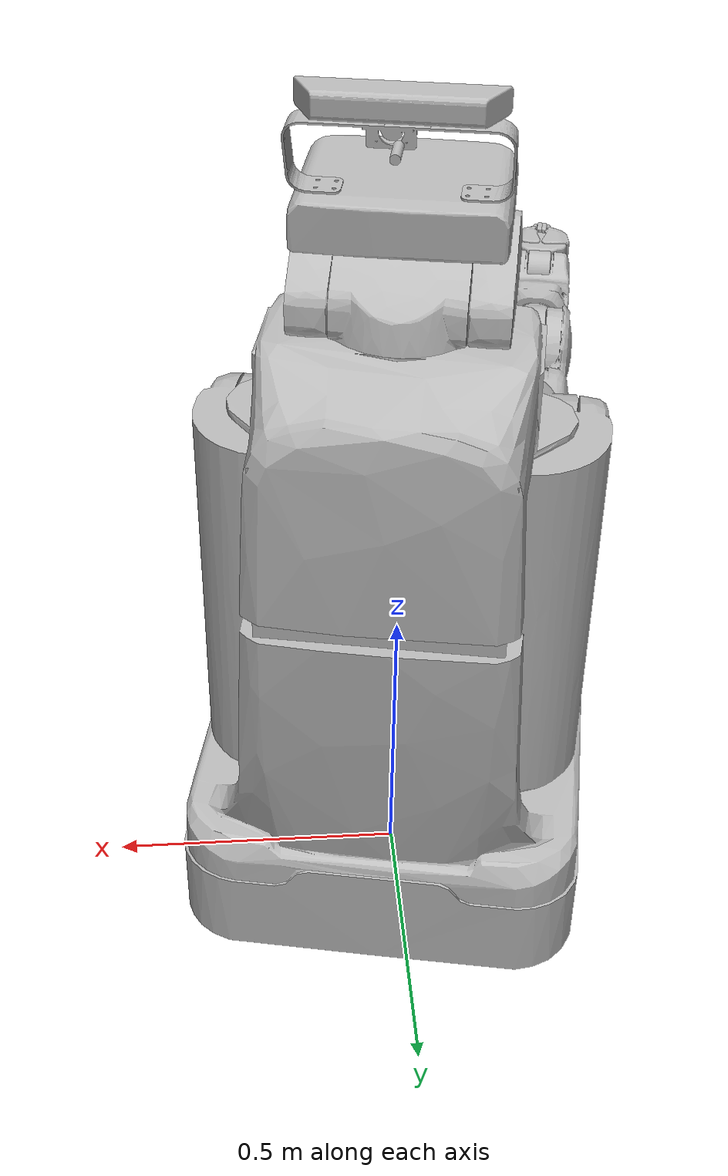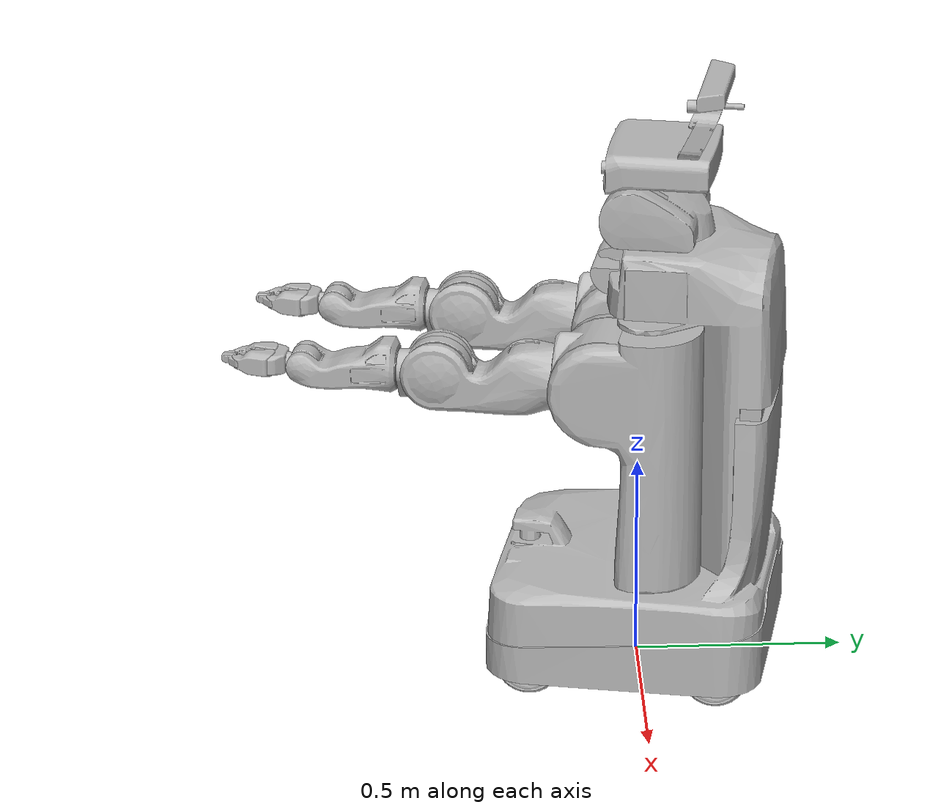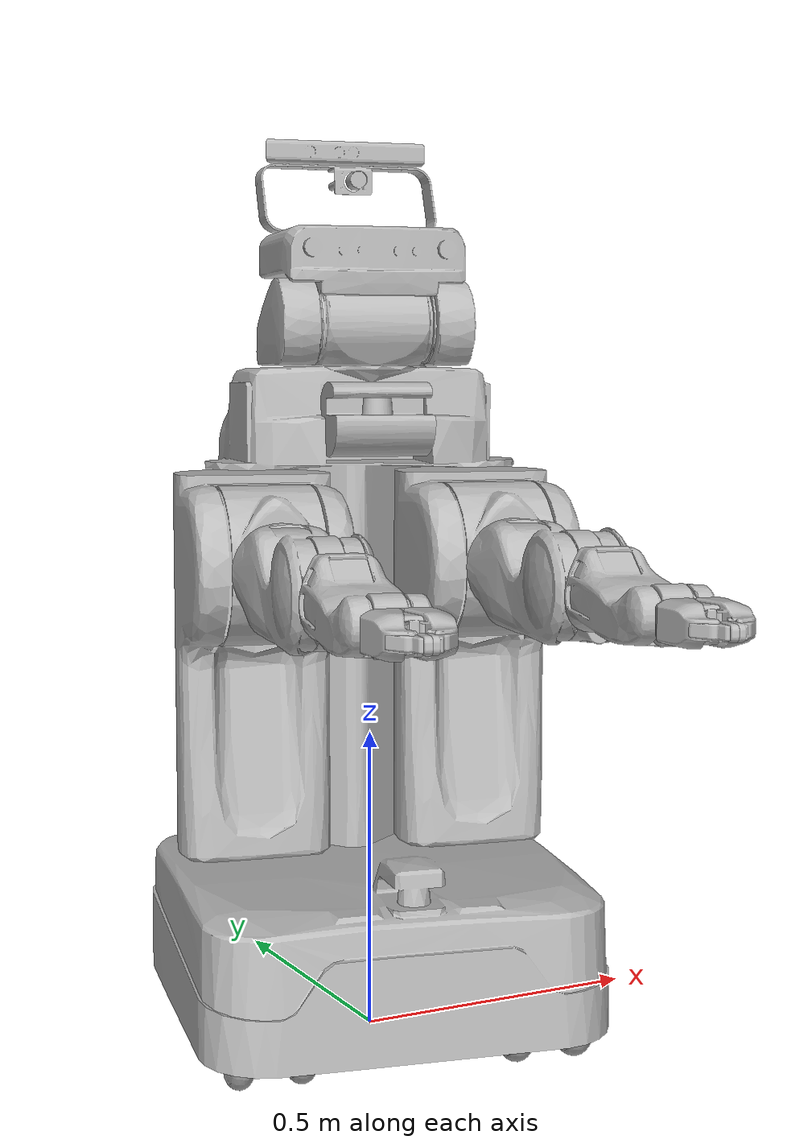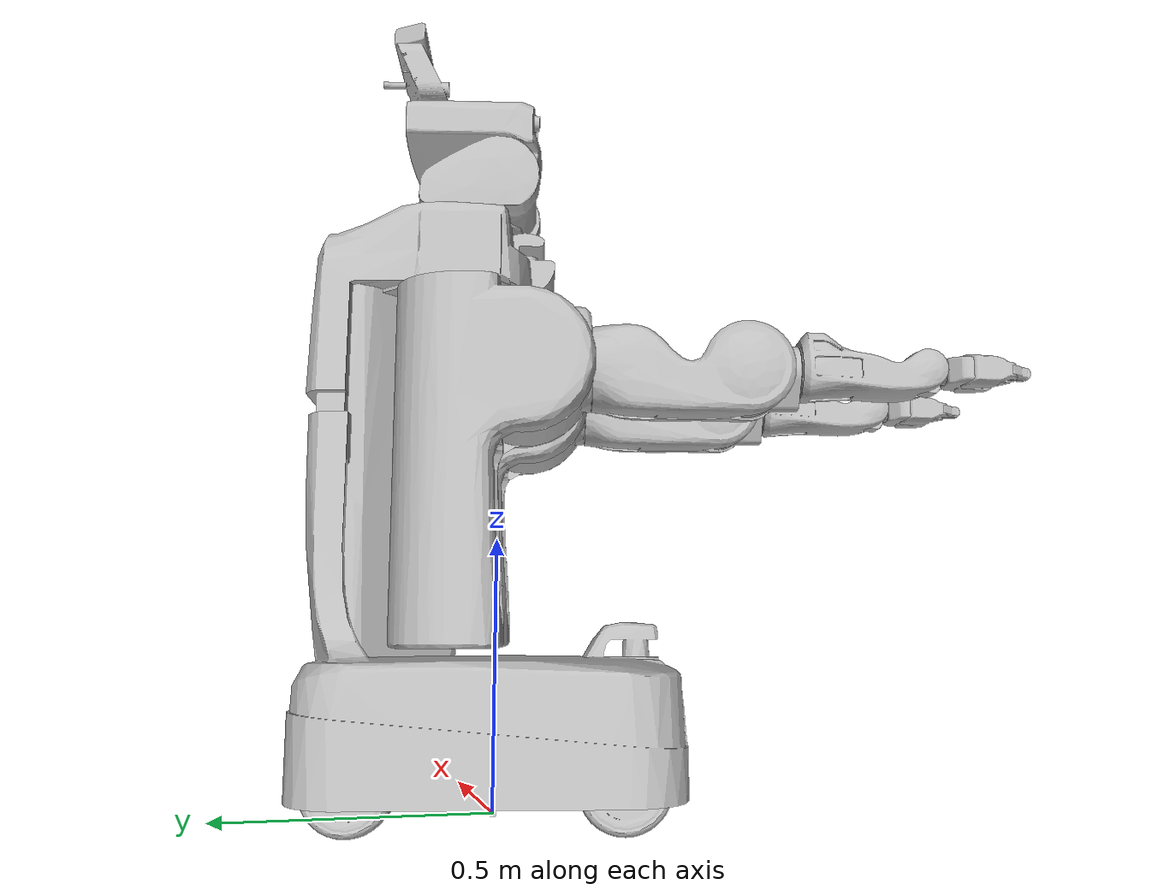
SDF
<?xml version='1.0'?>
<sdf version='1.6'>
  <model name='PR2'>
    <model name='pr2'>
      <static>0</static>
      <link name='base_footprint'>
        <self_collide>0</self_collide>
        <inertial>
          <mass>118.001</mass>
          <pose frame=''>-0.062421 0 0.201365 0 -0 0</pose>
          <inertia>
            <ixx>8.43173</ixx>
            <ixy>-0.00972</ixy>
            <ixz>1.90157</ixz>
            <iyy>8.53305</iyy>
            <iyz>-0.00738</iyz>
            <izz>3.78747</izz>
          </inertia>
        </inertial>
        <collision name='base_footprint_geom'>
          <pose frame=''>0 0 0.071 0 -0 0</pose>
          <geometry>
            <box>
              <size>0.001 0.001 0.001</size>
            </box>
          </geometry>
        </collision>
        <visual name='base_footprint_geom_visual'>
          <geometry>
            <box>
              <size>0.01 0.01 0.01</size>
            </box>
          </geometry>
        </visual>
        <collision name='base_footprint_geom_base_bellow_link'>
          <pose frame=''>-0.29 0 0.851 0 -0 0</pose>
          <geometry>
            <box>
              <size>0.05 0.37 0.3</size>
            </box>
          </geometry>
        </collision>
        <visual name='base_footprint_geom_base_bellow_link_visual'>
          <pose frame=''>-0.29 0 0.851 0 -0 0</pose>
          <geometry>
            <box>
              <size>0.05 0.37 0.3</size>
            </box>
          </geometry>
        </visual>
        <collision name='base_footprint_geom_base_link'>
          <pose frame=''>0 0 0.051 0 -0 0</pose>
          <geometry>
            <mesh>
              <uri>model://pr2/meshes/base_v0/base_L.stl</uri>
            </mesh>
          </geometry>
        </collision>
        <visual name='base_footprint_geom_base_link_visual'>
          <pose frame=''>0 0 0.051 0 -0 0</pose>
          <geometry>
            <mesh>
              <uri>model://pr2/meshes/base_v0/base.dae</uri>
            </mesh>
          </geometry>
        </visual>
        <sensor name='base_contact_sensor' type='contact'>
          <update_rate>100</update_rate>
          <contact>
            <collision>base_footprint_geom_base_link</collision>
            <topic>__default_topic__</topic>
          </contact>
          <plugin name='gazebo_contact' filename='libContactPlugin.so'/>
        </sensor>
        <sensor name='base_laser' type='ray'>
          <always_on>1</always_on>
          <visualize>1</visualize>
          <update_rate>20</update_rate>
          <pose frame=''>0.275 0 0.303 0 -0 0</pose>
          <ray>
            <scan>
              <horizontal>
                <samples>640</samples>
                <resolution>1</resolution>
                <min_angle>-2.2689</min_angle>
                <max_angle>2.2689</max_angle>
              </horizontal>
            </scan>
            <range>
              <min>0.08</min>
              <max>10</max>
              <resolution>0.01</resolution>
            </range>
          </ray>
          <plugin name='laser' filename='libRayPlugin.so'/>
        </sensor>
        <velocity_decay/>
      </link>
      <link name='bl_caster_rotation_link'>
        <self_collide>0</self_collide>
        <pose frame=''>-0.2246 0.2246 0.0792 0 -0 0</pose>
        <inertial>
          <mass>3.47308</mass>
          <pose frame=''>0 0 0.07 0 -0 0</pose>
          <inertia>
            <ixx>0.012412</ixx>
            <ixy>-0.000712</ixy>
            <ixz>0.000503</ixz>
            <iyy>0.015218</iyy>
            <iyz>-4e-06</iyz>
            <izz>0.011764</izz>
          </inertia>
        </inertial>
        <collision name='bl_caster_rotation_link_geom'>
          <geometry>
            <mesh>
              <uri>model://pr2/meshes/base_v0/caster_L.stl</uri>
            </mesh>
          </geometry>
        </collision>
        <visual name='bl_caster_rotation_link_geom_visual'>
          <geometry>
            <mesh>
              <uri>model://pr2/meshes/base_v0/caster.stl</uri>
            </mesh>
          </geometry>
        </visual>
        <velocity_decay/>
      </link>
      <link name='bl_caster_l_wheel_link'>
        <self_collide>0</self_collide>
        <pose frame=''>-0.2246 0.2736 0.0792 0 -0 0</pose>
        <inertial>
          <mass>0.44036</mass>
          <inertia>
            <ixx>0.012412</ixx>
            <ixy>-0.000712</ixy>
            <ixz>0.000503</ixz>
            <iyy>0.015218</iyy>
            <iyz>-4e-06</iyz>
            <izz>0.011764</izz>
          </inertia>
        </inertial>
        <collision name='bl_caster_l_wheel_link_geom'>
          <pose frame=''>0 0 0 1.5708 -0 0</pose>
          <geometry>
            <cylinder>
              <radius>0.074792</radius>
              <length>0.034</length>
            </cylinder>
          </geometry>
        </collision>
        <visual name='bl_caster_l_wheel_link_geom_visual'>
          <geometry>
            <mesh>
              <uri>model://pr2/meshes/base_v0/wheel.dae</uri>
            </mesh>
          </geometry>
        </visual>
        <velocity_decay/>
      </link>
      <link name='bl_caster_r_wheel_link'>
        <self_collide>0</self_collide>
        <pose frame=''>-0.2246 0.1756 0.0792 0 -0 0</pose>
        <inertial>
          <mass>0.44036</mass>
          <inertia>
            <ixx>0.012412</ixx>
            <ixy>0.000712</ixy>
            <ixz>0.000503</ixz>
            <iyy>0.015218</iyy>
            <iyz>4e-06</iyz>
            <izz>0.011764</izz>
          </inertia>
        </inertial>
        <collision name='bl_caster_r_wheel_link_geom'>
          <pose frame=''>0 0 0 1.5708 -0 0</pose>
          <geometry>
            <cylinder>
              <radius>0.074792</radius>
              <length>0.034</length>
            </cylinder>
          </geometry>
        </collision>
        <visual name='bl_caster_r_wheel_link_geom_visual'>
          <geometry>
            <mesh>
              <uri>model://pr2/meshes/base_v0/wheel.dae</uri>
            </mesh>
          </geometry>
        </visual>
        <velocity_decay/>
      </link>
      <link name='br_caster_rotation_link'>
        <self_collide>0</self_collide>
        <pose frame=''>-0.2246 -0.2246 0.0792 0 -0 0</pose>
        <inertial>
          <mass>3.47308</mass>
          <pose frame=''>0 0 0.07 0 -0 0</pose>
          <inertia>
            <ixx>0.012412</ixx>
            <ixy>-0.000712</ixy>
            <ixz>0.000503</ixz>
            <iyy>0.015218</iyy>
            <iyz>-4e-06</iyz>
            <izz>0.011764</izz>
          </inertia>
        </inertial>
        <collision name='br_caster_rotation_link_geom'>
          <geometry>
            <mesh>
              <uri>model://pr2/meshes/base_v0/caster_L.stl</uri>
            </mesh>
          </geometry>
        </collision>
        <visual name='br_caster_rotation_link_geom_visual'>
          <geometry>
            <mesh>
              <uri>model://pr2/meshes/base_v0/caster.stl</uri>
            </mesh>
          </geometry>
        </visual>
        <velocity_decay/>
      </link>
      <link name='br_caster_l_wheel_link'>
        <self_collide>0</self_collide>
        <pose frame=''>-0.2246 -0.1756 0.0792 0 -0 0</pose>
        <inertial>
          <mass>0.44036</mass>
          <inertia>
            <ixx>0.012412</ixx>
            <ixy>-0.000712</ixy>
            <ixz>0.000503</ixz>
            <iyy>0.015218</iyy>
            <iyz>-4e-06</iyz>
            <izz>0.011764</izz>
          </inertia>
        </inertial>
        <collision name='br_caster_l_wheel_link_geom'>
          <pose frame=''>0 0 0 1.5708 -0 0</pose>
          <geometry>
            <cylinder>
              <radius>0.074792</radius>
              <length>0.034</length>
            </cylinder>
          </geometry>
        </collision>
        <visual name='br_caster_l_wheel_link_geom_visual'>
          <geometry>
            <mesh>
              <uri>model://pr2/meshes/base_v0/wheel.dae</uri>
            </mesh>
          </geometry>
        </visual>
        <velocity_decay/>
      </link>
      <link name='br_caster_r_wheel_link'>
        <self_collide>0</self_collide>
        <pose frame=''>-0.2246 -0.2736 0.0792 0 -0 0</pose>
        <inertial>
          <mass>0.44036</mass>
          <inertia>
            <ixx>0.012412</ixx>
            <ixy>-0.000712</ixy>
            <ixz>0.000503</ixz>
            <iyy>0.015218</iyy>
            <iyz>-4e-06</iyz>
            <izz>0.011764</izz>
          </inertia>
        </inertial>
        <collision name='br_caster_r_wheel_link_geom'>
          <pose frame=''>0 0 0 1.5708 -0 0</pose>
          <geometry>
            <cylinder>
              <radius>0.074792</radius>
              <length>0.034</length>
            </cylinder>
          </geometry>
        </collision>
        <visual name='br_caster_r_wheel_link_geom_visual'>
          <geometry>
            <mesh>
              <uri>model://pr2/meshes/base_v0/wheel.dae</uri>
            </mesh>
          </geometry>
        </visual>
        <velocity_decay/>
      </link>
      <link name='fl_caster_rotation_link'>
        <self_collide>0</self_collide>
        <pose frame=''>0.2246 0.2246 0.0792 0 -0 0</pose>
        <inertial>
          <mass>3.47308</mass>
          <pose frame=''>0 0 0.07 0 -0 0</pose>
          <inertia>
            <ixx>0.012412</ixx>
            <ixy>-0.000712</ixy>
            <ixz>0.000503</ixz>
            <iyy>0.015218</iyy>
            <iyz>-4e-06</iyz>
            <izz>0.011764</izz>
          </inertia>
        </inertial>
        <collision name='fl_caster_rotation_link_geom'>
          <geometry>
            <mesh>
              <uri>model://pr2/meshes/base_v0/caster_L.stl</uri>
            </mesh>
          </geometry>
        </collision>
        <visual name='fl_caster_rotation_link_geom_visual'>
          <geometry>
            <mesh>
              <uri>model://pr2/meshes/base_v0/caster.stl</uri>
            </mesh>
          </geometry>
        </visual>
        <velocity_decay/>
      </link>
      <link name='fl_caster_l_wheel_link'>
        <self_collide>0</self_collide>
        <pose frame=''>0.2246 0.2736 0.0792 0 -0 0</pose>
        <inertial>
          <mass>0.44036</mass>
          <inertia>
            <ixx>0.012412</ixx>
            <ixy>-0.000712</ixy>
            <ixz>0.000503</ixz>
            <iyy>0.015218</iyy>
            <iyz>-4e-06</iyz>
            <izz>0.011764</izz>
          </inertia>
        </inertial>
        <collision name='fl_caster_l_wheel_link_geom'>
          <pose frame=''>0 0 0 1.5708 -0 0</pose>
          <geometry>
            <cylinder>
              <radius>0.074792</radius>
              <length>0.034</length>
            </cylinder>
          </geometry>
        </collision>
        <visual name='fl_caster_l_wheel_link_geom_visual'>
          <geometry>
            <mesh>
              <uri>model://pr2/meshes/base_v0/wheel.dae</uri>
            </mesh>
          </geometry>
        </visual>
        <velocity_decay/>
      </link>
      <link name='fl_caster_r_wheel_link'>
        <self_collide>0</self_collide>
        <pose frame=''>0.2246 0.1756 0.0792 0 -0 0</pose>
        <inertial>
          <mass>0.44036</mass>
          <inertia>
            <ixx>0.012412</ixx>
            <ixy>-0.000712</ixy>
            <ixz>0.000503</ixz>
            <iyy>0.015218</iyy>
            <iyz>-4e-06</iyz>
            <izz>0.011764</izz>
          </inertia>
        </inertial>
        <collision name='fl_caster_r_wheel_link_geom'>
          <pose frame=''>0 0 0 1.5708 -0 0</pose>
          <geometry>
            <cylinder>
              <radius>0.074792</radius>
              <length>0.034</length>
            </cylinder>
          </geometry>
        </collision>
        <visual name='fl_caster_r_wheel_link_geom_visual'>
          <geometry>
            <mesh>
              <uri>model://pr2/meshes/base_v0/wheel.dae</uri>
            </mesh>
          </geometry>
        </visual>
        <velocity_decay/>
      </link>
      <link name='fr_caster_rotation_link'>
        <self_collide>0</self_collide>
        <pose frame=''>0.2246 -0.2246 0.0792 0 -0 0</pose>
        <inertial>
          <mass>3.47308</mass>
          <pose frame=''>0 0 0.07 0 -0 0</pose>
          <inertia>
            <ixx>0.012412</ixx>
            <ixy>-0.000712</ixy>
            <ixz>0.000503</ixz>
            <iyy>0.015218</iyy>
            <iyz>-4e-06</iyz>
            <izz>0.011764</izz>
          </inertia>
        </inertial>
        <collision name='fr_caster_rotation_link_geom'>
          <geometry>
            <mesh>
              <uri>model://pr2/meshes/base_v0/caster_L.stl</uri>
            </mesh>
          </geometry>
        </collision>
        <visual name='fr_caster_rotation_link_geom_visual'>
          <geometry>
            <mesh>
              <uri>model://pr2/meshes/base_v0/caster.stl</uri>
            </mesh>
          </geometry>
        </visual>
        <velocity_decay/>
      </link>
      <link name='fr_caster_l_wheel_link'>
        <self_collide>0</self_collide>
        <pose frame=''>0.2246 -0.1756 0.0792 0 -0 0</pose>
        <inertial>
          <mass>0.44036</mass>
          <inertia>
            <ixx>0.012412</ixx>
            <ixy>-0.000712</ixy>
            <ixz>0.000503</ixz>
            <iyy>0.015218</iyy>
            <iyz>-4e-06</iyz>
            <izz>0.011764</izz>
          </inertia>
        </inertial>
        <collision name='fr_caster_l_wheel_link_geom'>
          <pose frame=''>0 0 0 1.5708 -0 0</pose>
          <geometry>
            <cylinder>
              <radius>0.074792</radius>
              <length>0.034</length>
            </cylinder>
          </geometry>
        </collision>
        <visual name='fr_caster_l_wheel_link_geom_visual'>
          <geometry>
            <mesh>
              <uri>model://pr2/meshes/base_v0/wheel.dae</uri>
            </mesh>
          </geometry>
        </visual>
        <velocity_decay/>
      </link>
      <link name='fr_caster_r_wheel_link'>
        <self_collide>0</self_collide>
        <pose frame=''>0.2246 -0.2736 0.0792 0 -0 0</pose>
        <inertial>
          <mass>0.44036</mass>
          <inertia>
            <ixx>0.012412</ixx>
            <ixy>-0.000712</ixy>
            <ixz>0.000503</ixz>
            <iyy>0.015218</iyy>
            <iyz>-4e-06</iyz>
            <izz>0.011764</izz>
          </inertia>
        </inertial>
        <collision name='fr_caster_r_wheel_link_geom'>
          <pose frame=''>0 0 0 1.5708 -0 0</pose>
          <geometry>
            <cylinder>
              <radius>0.074792</radius>
              <length>0.034</length>
            </cylinder>
          </geometry>
        </collision>
        <visual name='fr_caster_r_wheel_link_geom_visual'>
          <geometry>
            <mesh>
              <uri>model://pr2/meshes/base_v0/wheel.dae</uri>
            </mesh>
          </geometry>
        </visual>
        <velocity_decay/>
      </link>
      <link name='torso_lift_link'>
        <self_collide>0</self_collide>
        <pose frame=''>-0.05 0 0.790675 0 -0 0</pose>
        <inertial>
          <mass>36.449</mass>
          <pose frame=''>-0.099499 -4e-06 -0.086764 0 -0 0</pose>
          <inertia>
            <ixx>2.79233</ixx>
            <ixy>0.00428</ixy>
            <ixz>-0.160631</ixz>
            <iyy>2.52106</iyy>
            <iyz>0.029689</iyz>
            <izz>0.536551</izz>
          </inertia>
        </inertial>
        <collision name='torso_lift_link_geom'>
          <geometry>
            <mesh>
              <uri>model://pr2/meshes/torso_v0/torso_lift_L.stl</uri>
            </mesh>
          </geometry>
        </collision>
        <visual name='torso_lift_link_geom_visual'>
          <geometry>
            <mesh>
              <uri>model://pr2/meshes/torso_v0/torso_lift.dae</uri>
            </mesh>
          </geometry>
        </visual>
        <sensor name='torso_lift_contact_sensor' type='contact'>
          <update_rate>100</update_rate>
          <contact>
            <collision>torso_lift_link_geom</collision>
            <topic>__default_topic__</topic>
          </contact>
        </sensor>
        <velocity_decay/>
      </link>
      <link name='head_pan_link'>
        <self_collide>0</self_collide>
        <pose frame=''>-0.06707 0 1.17213 0 -0 0</pose>
        <inertial>
          <mass>6.339</mass>
          <pose frame=''>0.010907 0.031693 0.090507 0 -0 0</pose>
          <inertia>
            <ixx>0.032498</ixx>
            <ixy>0.000636</ixy>
            <ixz>0.002585</ixz>
            <iyy>0.046546</iyy>
            <iyz>-0.002453</iyz>
            <izz>0.057653</izz>
          </inertia>
        </inertial>
        <collision name='head_pan_link_geom'>
          <geometry>
            <mesh>
              <uri>model://pr2/meshes/head_v0/head_pan_L.stl</uri>
            </mesh>
          </geometry>
        </collision>
        <visual name='head_pan_link_geom_visual'>
          <geometry>
            <mesh>
              <uri>model://pr2/meshes/head_v0/head_pan.dae</uri>
            </mesh>
          </geometry>
        </visual>
        <velocity_decay/>
      </link>
      <link name='head_tilt_link'>
        <projector name='projector_wg6802418_projector_wg6802418'>
          <texture>stereo_projection_pattern_high_res_red.png</texture>
          <fov>0.959931</fov>
          <near_clip>0.1</near_clip>
          <far_clip>10</far_clip>
          <pose frame=''>0.0232 0.11 0.1191 0 -1.57079 0</pose>
        </projector>
        <self_collide>0</self_collide>
        <pose frame=''>0.00093 0 1.17213 0 -0 0</pose>
        <inertial>
          <mass>5.319</mass>
          <pose frame=''>-0.005151 -0.014635 0.072819 0 -0 0</pose>
          <inertia>
            <ixx>0.126134</ixx>
            <ixy>0.000237</ixy>
            <ixz>0.011881</ixz>
            <iyy>0.165102</iyy>
            <iyz>0.001606</iyz>
            <izz>0.166947</izz>
          </inertia>
        </inertial>
        <collision name='head_tilt_link_geom'>
          <geometry>
            <mesh>
              <uri>model://pr2/meshes/head_v0/head_tilt_L.stl</uri>
            </mesh>
          </geometry>
        </collision>
        <visual name='head_tilt_link_geom_visual'>
          <geometry>
            <mesh>
              <uri>model://pr2/meshes/head_v0/head_tilt.dae</uri>
            </mesh>
          </geometry>
        </visual>
        <collision name='head_tilt_link_geom_head_mount_kinect_ir_link'>
          <pose frame=''>-0.147067 0.0125 0.291953 0 -0 0</pose>
          <geometry>
            <sphere>
              <radius>0.0005</radius>
            </sphere>
          </geometry>
        </collision>
        <visual name='head_tilt_link_geom_head_mount_kinect_ir_link_visual'>
          <pose frame=''>-0.147067 0.0125 0.291953 0 -0 0</pose>
          <geometry>
            <sphere>
              <radius>0.00025</radius>
            </sphere>
          </geometry>
          <material>
            <script>
              <name>Gazebo/Red</name>
              <uri>__default__</uri>
            </script>
          </material>
        </visual>
        <collision name='head_tilt_link_geom_head_mount_kinect_rgb_link'>
          <pose frame=''>-0.147067 0.0175 0.291953 0 -0 0</pose>
          <geometry>
            <sphere>
              <radius>0.0005</radius>
            </sphere>
          </geometry>
        </collision>
        <visual name='head_tilt_link_geom_head_mount_kinect_rgb_link_visual'>
          <pose frame=''>-0.147067 0.0175 0.291953 0 -0 0</pose>
          <geometry>
            <sphere>
              <radius>0.00025</radius>
            </sphere>
          </geometry>
          <material>
            <script>
              <name>Gazebo/Red</name>
              <uri>__default__</uri>
            </script>
          </material>
        </visual>
        <collision name='head_tilt_link_geom_head_mount_link'>
          <pose frame=''>-0.1148 0 0.1555 0 -0 0</pose>
          <geometry>
            <sphere>
              <radius>0.0005</radius>
            </sphere>
          </geometry>
        </collision>
        <visual name='head_tilt_link_geom_head_mount_link_visual'>
          <pose frame=''>-0.1148 0 0.1555 0 -0 0</pose>
          <geometry>
            <mesh>
              <uri>model://pr2/meshes/sensors/kinect_prosilica_v0/115x100_swept_back--coarse.STL</uri>
              <scale>0.001 0.001 0.001</scale>
            </mesh>
          </geometry>
        </visual>
        <collision name='head_tilt_link_geom_head_mount_prosilica_link'>
          <pose frame=''>-0.161257 0.0125 0.244421 0 -0 0</pose>
          <geometry>
            <sphere>
              <radius>0.0005</radius>
            </sphere>
          </geometry>
        </collision>
        <visual name='head_tilt_link_geom_head_mount_prosilica_link_visual'>
          <pose frame=''>-0.161257 0.0125 0.244421 0 -0 0</pose>
          <geometry>
            <sphere>
              <radius>0.00025</radius>
            </sphere>
          </geometry>
          <material>
            <script>
              <name>Gazebo/Red</name>
              <uri>__default__</uri>
            </script>
          </material>
        </visual>
        <collision name='head_tilt_link_geom_head_plate_frame'>
          <pose frame=''>0.0232 0 0.0645 0 -0 0</pose>
          <geometry>
            <box>
              <size>0.01 0.01 0.01</size>
            </box>
          </geometry>
        </collision>
        <visual name='head_tilt_link_geom_head_plate_frame_visual'>
          <pose frame=''>0.0232 0 0.0645 0 -0 0</pose>
          <geometry>
            <box>
              <size>0.01 0.01 0.01</size>
            </box>
          </geometry>
          <material>
            <script>
              <name>Gazebo/Grey</name>
              <uri>__default__</uri>
            </script>
          </material>
        </visual>
        <sensor name='head_mount_sensor' type='camera'>
          <always_on>0</always_on>
          <visualize>0</visualize>
          <update_rate>1</update_rate>
          <pose frame=''>-0.147067 0.0125 0.291953 0 -0 0</pose>
          <camera name='__default__'>
            <horizontal_fov>0.994838</horizontal_fov>
            <image>
              <width>640</width>
              <height>480</height>
              <format>L8</format>
            </image>
            <clip>
              <near>0.01</near>
              <far>5</far>
            </clip>
          </camera>
        </sensor>
        <sensor name='head_mount_prosilica_link_sensor' type='camera'>
          <update_rate>1</update_rate>
          <pose frame=''>-0.161257 0.0125 0.244421 0 -0 0</pose>
          <camera name='__default__'>
            <horizontal_fov>1.1205</horizontal_fov>
            <image>
              <width>320</width>
              <height>240</height>
              <format>R8G8B8</format>
            </image>
            <clip>
              <near>0.1</near>
              <far>100</far>
            </clip>
          </camera>
        </sensor>
        <sensor name='head_mount_prosilica_link_sim_pcd_sensor' type='camera'>
          <update_rate>1</update_rate>
          <pose frame=''>-0.161257 0.0125 0.244421 0 -0 0</pose>
          <camera name='__default__'>
            <horizontal_fov>1.1205</horizontal_fov>
            <image>
              <width>320</width>
              <height>240</height>
              <format>R8G8B8</format>
            </image>
            <clip>
              <near>0.1</near>
              <far>100</far>
            </clip>
          </camera>
        </sensor>
        <sensor name='narrow_stereo_gazebo_l_stereo_camera_sensor' type='camera'>
          <always_on>1</always_on>
          <visualize>1</visualize>
          <update_rate>25</update_rate>
          <pose frame=''>0.0682 0.06 0.1146 0 -0 0</pose>
          <camera name='__default__'>
            <horizontal_fov>0.785398</horizontal_fov>
            <image>
              <width>640</width>
              <height>480</height>
              <format>L8</format>
            </image>
            <clip>
              <near>0.1</near>
              <far>100</far>
            </clip>
          </camera>
        </sensor>
        <sensor name='narrow_stereo_gazebo_r_stereo_camera_sensor' type='camera'>
          <always_on>1</always_on>
          <update_rate>25</update_rate>
          <pose frame=''>0.0682 -0.03 0.1146 0 -0 0</pose>
          <camera name='__default__'>
            <horizontal_fov>0.785398</horizontal_fov>
            <image>
              <width>640</width>
              <height>480</height>
              <format>L8</format>
            </image>
            <clip>
              <near>0.1</near>
              <far>100</far>
            </clip>
          </camera>
        </sensor>
        <sensor name='wide_stereo_gazebo_l_stereo_camera_sensor' type='camera'>
          <update_rate>25</update_rate>
          <pose frame=''>0.0682 0.03 0.1146 0 -0 0</pose>
          <camera name='__default__'>
            <horizontal_fov>1.5708</horizontal_fov>
            <image>
              <width>640</width>
              <height>480</height>
              <format>BAYER_BGGR8</format>
            </image>
            <clip>
              <near>0.1</near>
              <far>100</far>
            </clip>
          </camera>
        </sensor>
        <sensor name='wide_stereo_gazebo_r_stereo_camera_sensor' type='camera'>
          <update_rate>25</update_rate>
          <pose frame=''>0.0682 -0.06 0.1146 0 -0 0</pose>
          <camera name='__default__'>
            <horizontal_fov>1.5708</horizontal_fov>
            <image>
              <width>640</width>
              <height>480</height>
              <format>BAYER_BGGR8</format>
            </image>
            <clip>
              <near>0.1</near>
              <far>100</far>
            </clip>
          </camera>
        </sensor>
        <sensor name='high_def_sensor' type='camera'>
          <update_rate>20</update_rate>
          <pose frame=''>0.069657 -0.11 0.1191 0 -0 0</pose>
          <camera name='__default__'>
            <horizontal_fov>0.785398</horizontal_fov>
            <image>
              <width>2448</width>
              <height>2050</height>
              <format>R8G8B8</format>
            </image>
            <clip>
              <near>0.1</near>
              <far>100</far>
            </clip>
          </camera>
        </sensor>
        <velocity_decay/>
      </link>
      <link name='l_shoulder_pan_link'>
        <self_collide>0</self_collide>
        <gravity>0</gravity>
        <pose frame=''>-0.05 0.188 0.790675 0 -0 0</pose>
        <inertial>
          <mass>25.7993</mass>
          <pose frame=''>-0.001201 0.024513 -0.098231 0 -0 0</pose>
          <inertia>
            <ixx>0.866179</ixx>
            <ixy>-0.060865</ixy>
            <ixz>-0.121181</ixz>
            <iyy>0.874217</iyy>
            <iyz>-0.058866</iyz>
            <izz>0.273538</izz>
          </inertia>
        </inertial>
        <collision name='l_shoulder_pan_link_geom'>
          <geometry>
            <mesh>
              <uri>model://pr2/meshes/shoulder_v0/shoulder_pan.stl</uri>
            </mesh>
          </geometry>
        </collision>
        <visual name='l_shoulder_pan_link_geom_visual'>
          <geometry>
            <mesh>
              <uri>model://pr2/meshes/shoulder_v0/shoulder_pan.dae</uri>
            </mesh>
          </geometry>
        </visual>
        <velocity_decay/>
      </link>
      <link name='l_shoulder_lift_link'>
        <self_collide>0</self_collide>
        <gravity>0</gravity>
        <pose frame=''>0.05 0.188 0.790675 0 -0 0</pose>
        <inertial>
          <mass>2.74988</mass>
          <pose frame=''>0.02195 -0.02664 -0.03127 0 -0 0</pose>
          <inertia>
            <ixx>0.021056</ixx>
            <ixy>0.004967</ixy>
            <ixz>-0.001948</ixz>
            <iyy>0.021272</iyy>
            <iyz>0.001104</iyz>
            <izz>0.019758</izz>
          </inertia>
        </inertial>
        <collision name='l_shoulder_lift_link_geom'>
          <geometry>
            <mesh>
              <uri>model://pr2/meshes/shoulder_v0/shoulder_lift.stl</uri>
            </mesh>
          </geometry>
        </collision>
        <visual name='l_shoulder_lift_link_geom_visual'>
          <geometry>
            <mesh>
              <uri>model://pr2/meshes/shoulder_v0/shoulder_lift.dae</uri>
            </mesh>
          </geometry>
        </visual>
        <velocity_decay/>
      </link>
      <link name='l_upper_arm_roll_link'>
        <self_collide>0</self_collide>
        <gravity>0</gravity>
        <pose frame=''>0.05 0.188 0.790675 0 -0 0</pose>
        <inertial>
          <mass>6.11769</mass>
          <pose frame=''>0.210551 0.016309 -0.000561 0 -0 0</pose>
          <inertia>
            <ixx>0.025306</ixx>
            <ixy>-0.003393</ixy>
            <ixz>0.000608</ixz>
            <iyy>0.084737</iyy>
            <iyz>-0.0002</iyz>
            <izz>0.086016</izz>
          </inertia>
        </inertial>
        <collision name='l_upper_arm_roll_link_geom'>
          <geometry>
            <mesh>
              <uri>model://pr2/meshes/shoulder_v0/upper_arm_roll_L.stl</uri>
            </mesh>
          </geometry>
        </collision>
        <visual name='l_upper_arm_roll_link_geom_visual'>
          <geometry>
            <mesh>
              <uri>model://pr2/meshes/shoulder_v0/upper_arm_roll.stl</uri>
            </mesh>
          </geometry>
        </visual>
        <collision name='l_upper_arm_roll_link_geom_l_upper_arm_link'>
          <geometry>
            <mesh>
              <uri>model://pr2/meshes/upper_arm_v0/upper_arm.stl</uri>
            </mesh>
          </geometry>
        </collision>
        <visual name='l_upper_arm_roll_link_geom_l_upper_arm_link_visual'>
          <geometry>
            <mesh>
              <uri>model://pr2/meshes/upper_arm_v0/upper_arm.dae</uri>
            </mesh>
          </geometry>
        </visual>
        <velocity_decay/>
      </link>
      <link name='l_elbow_flex_link'>
        <self_collide>0</self_collide>
        <gravity>0</gravity>
        <pose frame=''>0.45 0.188 0.790675 0 -0 0</pose>
        <inertial>
          <mass>1.90327</mass>
          <pose frame=''>0.01014 0.00032 -0.01211 0 -0 0</pose>
          <inertia>
            <ixx>0.003465</ixx>
            <ixy>4.1e-05</ixy>
            <ixz>0.000432</ixz>
            <iyy>0.004416</iyy>
            <iyz>-4e-05</iyz>
            <izz>0.003592</izz>
          </inertia>
        </inertial>
        <collision name='l_elbow_flex_link_geom'>
          <geometry>
            <mesh>
              <uri>model://pr2/meshes/upper_arm_v0/elbow_flex.stl</uri>
            </mesh>
          </geometry>
        </collision>
        <visual name='l_elbow_flex_link_geom_visual'>
          <geometry>
            <mesh>
              <uri>model://pr2/meshes/upper_arm_v0/elbow_flex.dae</uri>
            </mesh>
          </geometry>
        </visual>
        <velocity_decay/>
      </link>
      <link name='l_forearm_roll_link'>
        <self_collide>0</self_collide>
        <gravity>0</gravity>
        <pose frame=''>0.45 0.188 0.790675 0 -0 0</pose>
        <inertial>
          <mass>2.68968</mass>
          <pose frame=''>0.180727 -0.000163 -0.008583 0 -0 0</pose>
          <inertia>
            <ixx>0.014668</ixx>
            <ixy>5.2e-05</ixy>
            <ixz>0.000656</ixz>
            <iyy>0.026279</iyy>
            <iyz>-1.3e-05</iyz>
            <izz>0.027775</izz>
          </inertia>
        </inertial>
        <collision name='l_forearm_roll_link_geom'>
          <geometry>
            <mesh>
              <uri>model://pr2/meshes/upper_arm_v0/forearm_roll_L.stl</uri>
            </mesh>
          </geometry>
        </collision>
        <visual name='l_forearm_roll_link_geom_visual'>
          <geometry>
            <mesh>
              <uri>model://pr2/meshes/upper_arm_v0/forearm_roll.stl</uri>
            </mesh>
          </geometry>
        </visual>
        <collision name='l_forearm_roll_link_geom_l_forearm_link'>
          <geometry>
            <mesh>
              <uri>model://pr2/meshes/forearm_v0/forearm.stl</uri>
            </mesh>
          </geometry>
        </collision>
        <visual name='l_forearm_roll_link_geom_l_forearm_link_visual'>
          <geometry>
            <mesh>
              <uri>model://pr2/meshes/forearm_v0/forearm.dae</uri>
            </mesh>
          </geometry>
        </visual>
        <sensor name='l_forearm_cam_sensor' type='camera'>
          <update_rate>25</update_rate>
          <pose frame=''>0.135 0 0.044 -1.5708 -0.562869 0</pose>
          <camera name='__default__'>
            <horizontal_fov>1.5708</horizontal_fov>
            <image>
              <width>640</width>
              <height>480</height>
              <format>R8G8B8</format>
            </image>
            <clip>
              <near>0.1</near>
              <far>100</far>
            </clip>
          </camera>
        </sensor>
        <velocity_decay/>
      </link>
      <link name='l_wrist_flex_link'>
        <self_collide>0</self_collide>
        <gravity>0</gravity>
        <pose frame=''>0.771 0.188 0.790675 0 -0 0</pose>
        <inertial>
          <mass>0.61402</mass>
          <pose frame=''>-0.00157 0 -0.00075 0 -0 0</pose>
          <inertia>
            <ixx>0.000652</ixx>
            <ixy>0</ixy>
            <ixz>3e-06</ixz>
            <iyy>0.000198</iyy>
            <iyz>0</iyz>
            <izz>0.000645</izz>
          </inertia>
        </inertial>
        <collision name='l_wrist_flex_link_geom'>
          <geometry>
            <mesh>
              <uri>model://pr2/meshes/forearm_v0/wrist_flex.stl</uri>
            </mesh>
          </geometry>
        </collision>
        <visual name='l_wrist_flex_link_geom_visual'>
          <geometry>
            <mesh>
              <uri>model://pr2/meshes/forearm_v0/wrist_flex.dae</uri>
            </mesh>
          </geometry>
        </visual>
        <velocity_decay/>
      </link>
      <link name='l_wrist_roll_link'>
        <self_collide>0</self_collide>
        <gravity>0</gravity>
        <pose frame=''>0.771 0.188 0.790675 0 -0 0</pose>
        <inertial>
          <mass>0.68107</mass>
          <pose frame=''>0.056408 0.000451 -0.001014 0 -0 0</pose>
          <inertia>
            <ixx>0.011352</ixx>
            <ixy>-1.6e-05</ixy>
            <ixz>-1e-06</ixz>
            <iyy>0.011677</iyy>
            <iyz>-1e-06</iyz>
            <izz>0.011866</izz>
          </inertia>
        </inertial>
        <collision name='l_wrist_roll_link_geom'>
          <geometry>
            <mesh>
              <uri>model://pr2/meshes/forearm_v0/wrist_roll_L.stl</uri>
            </mesh>
          </geometry>
        </collision>
        <visual name='l_wrist_roll_link_geom_visual'>
          <geometry>
            <mesh>
              <uri>model://pr2/meshes/forearm_v0/wrist_roll.stl</uri>
            </mesh>
          </geometry>
        </visual>
        <collision name='l_wrist_roll_link_geom_l_gripper_motor_accelerometer_link'>
          <geometry>
            <box>
              <size>0.001 0.001 0.001</size>
            </box>
          </geometry>
        </collision>
        <visual name='l_wrist_roll_link_geom_l_gripper_motor_accelerometer_link_visual'>
          <geometry>
            <box>
              <size>0.001 0.001 0.001</size>
            </box>
          </geometry>
        </visual>
        <collision name='l_wrist_roll_link_geom_l_gripper_palm_link'>
          <geometry>
            <mesh>
              <uri>model://pr2/meshes/gripper_v0/gripper_palm.stl</uri>
            </mesh>
          </geometry>
        </collision>
        <visual name='l_wrist_roll_link_geom_l_gripper_palm_link_visual'>
          <geometry>
            <mesh>
              <uri>model://pr2/meshes/gripper_v0/gripper_palm.dae</uri>
            </mesh>
          </geometry>
        </visual>
        <velocity_decay/>
      </link>
      <link name='l_gripper_l_finger_link'>
        <self_collide>0</self_collide>
        <gravity>0</gravity>
        <pose frame=''>0.84791 0.198 0.790675 0 -0 0</pose>
        <inertial>
          <mass>0.17126</mass>
          <pose frame=''>0.03598 0.0173 -0.00164 0 -0 0</pose>
          <inertia>
            <ixx>7.8e-05</ixx>
            <ixy>1e-06</ixy>
            <ixz>-1e-05</ixz>
            <iyy>0.000197</iyy>
            <iyz>-3e-06</iyz>
            <izz>0.000181</izz>
          </inertia>
        </inertial>
        <collision name='l_gripper_l_finger_link_geom'>
          <geometry>
            <mesh>
              <uri>model://pr2/meshes/gripper_v0/l_finger.stl</uri>
            </mesh>
          </geometry>
          <surface>
            <friction>
              <ode>
                <mu>500</mu>
                <mu2>500</mu2>
                <slip1>0</slip1>
                <slip2>0</slip2>
              </ode>
            </friction>
            <contact>
              <ode>
                <kp>1e+06</kp>
                <kd>1</kd>
                <max_vel>100</max_vel>
                <min_depth>0</min_depth>
              </ode>
            </contact>
          </surface>
        </collision>
        <visual name='l_gripper_l_finger_link_geom_visual'>
          <geometry>
            <mesh>
              <uri>model://pr2/meshes/gripper_v0/l_finger.dae</uri>
            </mesh>
          </geometry>
        </visual>
        <velocity_decay/>
      </link>
      <link name='l_gripper_l_finger_tip_link'>
        <self_collide>0</self_collide>
        <gravity>0</gravity>
        <pose frame=''>0.93928 0.20295 0.790675 0 -0 0</pose>
        <inertial>
          <mass>0.04419</mass>
          <pose frame=''>0.00423 0.00284 0 0 -0 0</pose>
          <inertia>
            <ixx>8e-06</ixx>
            <ixy>6e-06</ixy>
            <ixz>0</ixz>
            <iyy>1e-05</iyy>
            <iyz>0</iyz>
            <izz>1.5e-05</izz>
          </inertia>
        </inertial>
        <collision name='l_gripper_l_finger_tip_link_geom'>
          <geometry>
            <mesh>
              <uri>model://pr2/meshes/gripper_v0/l_finger_tip.stl</uri>
            </mesh>
          </geometry>
          <surface>
            <friction>
              <ode>
                <mu>500</mu>
                <mu2>500</mu2>
                <slip1>0</slip1>
                <slip2>0</slip2>
              </ode>
            </friction>
            <contact>
              <ode>
                <kp>1e+07</kp>
                <kd>1</kd>
                <max_vel>100</max_vel>
                <min_depth>0</min_depth>
              </ode>
            </contact>
          </surface>
        </collision>
        <visual name='l_gripper_l_finger_tip_link_geom_visual'>
          <geometry>
            <mesh>
              <uri>model://pr2/meshes/gripper_v0/l_finger_tip.dae</uri>
            </mesh>
          </geometry>
        </visual>
        <sensor name='l_gripper_l_finger_tip_contact_sensor' type='contact'>
          <update_rate>100</update_rate>
          <contact>
            <collision>l_gripper_l_finger_tip_link_geom</collision>
            <topic>__default_topic__</topic>
          </contact>
        </sensor>
        <velocity_decay/>
      </link>
      <link name='l_gripper_motor_slider_link'>
        <self_collide>0</self_collide>
        <gravity>0</gravity>
        <pose frame=''>0.93928 0.188 0.790675 0 -0 0</pose>
        <inertial>
          <mass>0.01</mass>
          <inertia>
            <ixx>0.001</ixx>
            <ixy>0</ixy>
            <ixz>0</ixz>
            <iyy>0.001</iyy>
            <iyz>0</iyz>
            <izz>0.001</izz>
          </inertia>
        </inertial>
        <velocity_decay/>
      </link>
      <link name='l_gripper_motor_screw_link'>
        <self_collide>0</self_collide>
        <gravity>0</gravity>
        <pose frame=''>0.93928 0.188 0.790675 0 -0 0</pose>
        <inertial>
          <mass>0.01</mass>
          <inertia>
            <ixx>0.0001</ixx>
            <ixy>0</ixy>
            <ixz>0</ixz>
            <iyy>0.0001</iyy>
            <iyz>0</iyz>
            <izz>0.0001</izz>
          </inertia>
        </inertial>
        <velocity_decay/>
      </link>
      <link name='l_gripper_r_finger_link'>
        <self_collide>0</self_collide>
        <gravity>0</gravity>
        <pose frame=''>0.84791 0.178 0.790675 0 -0 0</pose>
        <inertial>
          <mass>0.17389</mass>
          <pose frame=''>0.03576 -0.01736 -0.00095 0 -0 0</pose>
          <inertia>
            <ixx>7.7e-05</ixx>
            <ixy>-2e-06</ixy>
            <ixz>-8e-06</ixz>
            <iyy>0.000198</iyy>
            <iyz>2e-06</iyz>
            <izz>0.000181</izz>
          </inertia>
        </inertial>
        <collision name='l_gripper_r_finger_link_geom'>
          <pose frame=''>0 0 0 -3.14159 0 0</pose>
          <geometry>
            <mesh>
              <uri>model://pr2/meshes/gripper_v0/l_finger.stl</uri>
            </mesh>
          </geometry>
          <surface>
            <friction>
              <ode>
                <mu>500</mu>
                <mu2>500</mu2>
                <slip1>0</slip1>
                <slip2>0</slip2>
              </ode>
            </friction>
            <contact>
              <ode>
                <kp>1e+06</kp>
                <kd>1</kd>
                <max_vel>100</max_vel>
                <min_depth>0</min_depth>
              </ode>
            </contact>
          </surface>
        </collision>
        <visual name='l_gripper_r_finger_link_geom_visual'>
          <pose frame=''>0 0 0 -3.14159 0 0</pose>
          <geometry>
            <mesh>
              <uri>model://pr2/meshes/gripper_v0/l_finger.dae</uri>
            </mesh>
          </geometry>
        </visual>
        <velocity_decay/>
      </link>
      <link name='l_gripper_r_finger_tip_link'>
        <self_collide>0</self_collide>
        <gravity>0</gravity>
        <pose frame=''>0.93928 0.17305 0.790675 0 -0 0</pose>
        <inertial>
          <mass>0.04419</mass>
          <pose frame=''>0.00423 -0.00284 0 0 -0 0</pose>
          <inertia>
            <ixx>8e-06</ixx>
            <ixy>-6e-06</ixy>
            <ixz>0</ixz>
            <iyy>1e-05</iyy>
            <iyz>0</iyz>
            <izz>1.5e-05</izz>
          </inertia>
        </inertial>
        <collision name='l_gripper_r_finger_tip_link_geom'>
          <pose frame=''>0 0 0 -3.14159 0 0</pose>
          <geometry>
            <mesh>
              <uri>model://pr2/meshes/gripper_v0/l_finger_tip.stl</uri>
            </mesh>
          </geometry>
          <surface>
            <friction>
              <ode>
                <mu>500</mu>
                <mu2>500</mu2>
                <slip1>0</slip1>
                <slip2>0</slip2>
              </ode>
            </friction>
            <contact>
              <ode>
                <kp>1e+07</kp>
                <kd>1</kd>
                <max_vel>100</max_vel>
                <min_depth>0</min_depth>
              </ode>
            </contact>
          </surface>
        </collision>
        <visual name='l_gripper_r_finger_tip_link_geom_visual'>
          <pose frame=''>0 0 0 -3.14159 0 0</pose>
          <geometry>
            <mesh>
              <uri>model://pr2/meshes/gripper_v0/l_finger_tip.dae</uri>
            </mesh>
          </geometry>
        </visual>
        <sensor name='l_gripper_r_finger_tip_contact_sensor' type='contact'>
          <update_rate>100</update_rate>
          <contact>
            <collision>l_gripper_r_finger_tip_link_geom</collision>
            <topic>__default_topic__</topic>
          </contact>
        </sensor>
        <velocity_decay/>
      </link>
      <link name='laser_tilt_mount_link'>
        <self_collide>0</self_collide>
        <pose frame=''>0.04893 0 1.01768 0 -0 0</pose>
        <inertial>
          <mass>0.592</mass>
          <pose frame=''>-0.001134 0.001667 -0.007067 0 -0 0</pose>
          <inertia>
            <ixx>0.001296</ixx>
            <ixy>2.3e-05</ixy>
            <ixz>3.7e-05</ixz>
            <iyy>0.001086</iyy>
            <iyz>3.5e-05</iyz>
            <izz>0.000895</izz>
          </inertia>
        </inertial>
        <collision name='laser_tilt_mount_link_geom'>
          <geometry>
            <mesh>
              <uri>model://pr2/meshes/tilting_laser_v0/tilting_hokuyo_L.stl</uri>
            </mesh>
          </geometry>
          <surface>
            <friction>
              <ode>
                <mu>0</mu>
                <mu2>0</mu2>
                <slip1>0</slip1>
                <slip2>0</slip2>
              </ode>
            </friction>
            <contact>
              <ode>
                <kp>1e+12</kp>
                <kd>10000</kd>
                <max_vel>100</max_vel>
                <min_depth>0</min_depth>
              </ode>
            </contact>
          </surface>
        </collision>
        <visual name='laser_tilt_mount_link_geom_visual'>
          <geometry>
            <mesh>
              <uri>model://pr2/meshes/tilting_laser_v0/tilting_hokuyo.dae</uri>
            </mesh>
          </geometry>
        </visual>
        <sensor name='laser_tilt' type='ray'>
          <update_rate>40</update_rate>
          <pose frame=''>0 0 0.03 0 -0 0</pose>
          <ray>
            <scan>
              <horizontal>
                <samples>640</samples>
                <resolution>1</resolution>
                <min_angle>-1.39626</min_angle>
                <max_angle>1.39626</max_angle>
              </horizontal>
            </scan>
            <range>
              <min>0.08</min>
              <max>10</max>
              <resolution>0.01</resolution>
            </range>
          </ray>
        </sensor>
        <velocity_decay/>
      </link>
      <link name='r_shoulder_pan_link'>
        <self_collide>0</self_collide>
        <gravity>0</gravity>
        <pose frame=''>-0.05 -0.188 0.790675 0 -0 0</pose>
        <inertial>
          <mass>25.7993</mass>
          <pose frame=''>-0.001201 0.024513 -0.098231 0 -0 0</pose>
          <inertia>
            <ixx>0.866179</ixx>
            <ixy>-0.060865</ixy>
            <ixz>-0.121181</ixz>
            <iyy>0.874217</iyy>
            <iyz>-0.058866</iyz>
            <izz>0.273538</izz>
          </inertia>
        </inertial>
        <collision name='r_shoulder_pan_link_geom'>
          <geometry>
            <mesh>
              <uri>model://pr2/meshes/shoulder_v0/shoulder_pan.stl</uri>
            </mesh>
          </geometry>
          <surface>
            <friction>
              <ode>
                <mu>0</mu>
                <mu2>0</mu2>
                <slip1>0</slip1>
                <slip2>0</slip2>
              </ode>
            </friction>
            <contact>
              <ode>
                <kp>1e+12</kp>
                <kd>10000</kd>
                <max_vel>100</max_vel>
                <min_depth>0</min_depth>
              </ode>
            </contact>
          </surface>
        </collision>
        <visual name='r_shoulder_pan_link_geom_visual'>
          <geometry>
            <mesh>
              <uri>model://pr2/meshes/shoulder_v0/shoulder_pan.dae</uri>
            </mesh>
          </geometry>
        </visual>
        <velocity_decay/>
      </link>
      <link name='r_shoulder_lift_link'>
        <self_collide>0</self_collide>
        <gravity>0</gravity>
        <pose frame=''>0.05 -0.188 0.790675 0 -0 0</pose>
        <inertial>
          <mass>2.74988</mass>
          <pose frame=''>0.02195 -0.02664 -0.03127 0 -0 0</pose>
          <inertia>
            <ixx>0.021056</ixx>
            <ixy>0.004967</ixy>
            <ixz>-0.001948</ixz>
            <iyy>0.021272</iyy>
            <iyz>0.001104</iyz>
            <izz>0.019758</izz>
          </inertia>
        </inertial>
        <collision name='r_shoulder_lift_link_geom'>
          <geometry>
            <mesh>
              <uri>model://pr2/meshes/shoulder_v0/shoulder_lift.stl</uri>
            </mesh>
          </geometry>
          <surface>
            <friction>
              <ode>
                <mu>0</mu>
                <mu2>0</mu2>
                <slip1>0</slip1>
                <slip2>0</slip2>
              </ode>
            </friction>
            <contact>
              <ode>
                <kp>1e+12</kp>
                <kd>10000</kd>
                <max_vel>100</max_vel>
                <min_depth>0</min_depth>
              </ode>
            </contact>
          </surface>
        </collision>
        <visual name='r_shoulder_lift_link_geom_visual'>
          <geometry>
            <mesh>
              <uri>model://pr2/meshes/shoulder_v0/shoulder_lift.dae</uri>
            </mesh>
          </geometry>
        </visual>
        <velocity_decay/>
      </link>
      <link name='r_upper_arm_roll_link'>
        <self_collide>0</self_collide>
        <gravity>0</gravity>
        <pose frame=''>0.05 -0.188 0.790675 0 -0 0</pose>
        <inertial>
          <mass>6.11769</mass>
          <pose frame=''>0.210482 -0.015945 -0.000197 0 -0 0</pose>
          <inertia>
            <ixx>0.025378</ixx>
            <ixy>0.003757</ixy>
            <ixz>-0.000709</ixz>
            <iyy>0.084737</iyy>
            <iyz>-0.000179</iyz>
            <izz>0.086088</izz>
          </inertia>
        </inertial>
        <collision name='r_upper_arm_roll_link_geom'>
          <geometry>
            <mesh>
              <uri>model://pr2/meshes/shoulder_v0/upper_arm_roll_L.stl</uri>
            </mesh>
          </geometry>
        </collision>
        <visual name='r_upper_arm_roll_link_geom_visual'>
          <geometry>
            <mesh>
              <uri>model://pr2/meshes/shoulder_v0/upper_arm_roll.stl</uri>
            </mesh>
          </geometry>
        </visual>
        <collision name='r_upper_arm_roll_link_geom_r_upper_arm_link'>
          <geometry>
            <mesh>
              <uri>model://pr2/meshes/upper_arm_v0/upper_arm.stl</uri>
            </mesh>
          </geometry>
        </collision>
        <visual name='r_upper_arm_roll_link_geom_r_upper_arm_link_visual'>
          <geometry>
            <mesh>
              <uri>model://pr2/meshes/upper_arm_v0/upper_arm.dae</uri>
            </mesh>
          </geometry>
        </visual>
        <velocity_decay/>
      </link>
      <link name='r_elbow_flex_link'>
        <self_collide>0</self_collide>
        <gravity>0</gravity>
        <pose frame=''>0.45 -0.188 0.790675 0 -0 0</pose>
        <inertial>
          <mass>1.90327</mass>
          <pose frame=''>0.01014 0.00032 -0.01211 0 -0 0</pose>
          <inertia>
            <ixx>0.003465</ixx>
            <ixy>4.1e-05</ixy>
            <ixz>0.000432</ixz>
            <iyy>0.004416</iyy>
            <iyz>-4e-05</iyz>
            <izz>0.003592</izz>
          </inertia>
        </inertial>
        <collision name='r_elbow_flex_link_geom'>
          <geometry>
            <mesh>
              <uri>model://pr2/meshes/upper_arm_v0/elbow_flex.stl</uri>
            </mesh>
          </geometry>
        </collision>
        <visual name='r_elbow_flex_link_geom_visual'>
          <geometry>
            <mesh>
              <uri>model://pr2/meshes/upper_arm_v0/elbow_flex.dae</uri>
            </mesh>
          </geometry>
        </visual>
        <velocity_decay/>
      </link>
      <link name='r_forearm_roll_link'>
        <self_collide>0</self_collide>
        <gravity>0</gravity>
        <pose frame=''>0.45 -0.188 0.790675 0 -0 0</pose>
        <inertial>
          <mass>2.68968</mass>
          <pose frame=''>0.180727 -0.000163 -0.008583 0 -0 0</pose>
          <inertia>
            <ixx>0.014668</ixx>
            <ixy>5.2e-05</ixy>
            <ixz>0.000656</ixz>
            <iyy>0.026279</iyy>
            <iyz>-1.3e-05</iyz>
            <izz>0.027775</izz>
          </inertia>
        </inertial>
        <collision name='r_forearm_roll_link_geom'>
          <geometry>
            <mesh>
              <uri>model://pr2/meshes/upper_arm_v0/forearm_roll_L.stl</uri>
            </mesh>
          </geometry>
        </collision>
        <visual name='r_forearm_roll_link_geom_visual'>
          <geometry>
            <mesh>
              <uri>model://pr2/meshes/upper_arm_v0/forearm_roll.stl</uri>
            </mesh>
          </geometry>
        </visual>
        <collision name='r_forearm_roll_link_geom_r_forearm_link'>
          <geometry>
            <mesh>
              <uri>model://pr2/meshes/forearm_v0/forearm.stl</uri>
            </mesh>
          </geometry>
        </collision>
        <visual name='r_forearm_roll_link_geom_r_forearm_link_visual'>
          <geometry>
            <mesh>
              <uri>model://pr2/meshes/forearm_v0/forearm.dae</uri>
            </mesh>
          </geometry>
        </visual>
        <sensor name='r_forearm_cam_sensor' type='camera'>
          <update_rate>25</update_rate>
          <pose frame=''>0.135 0 0.044 1.5708 -0.562869 -0</pose>
          <camera name='__default__'>
            <horizontal_fov>1.5708</horizontal_fov>
            <image>
              <width>640</width>
              <height>480</height>
              <format>R8G8B8</format>
            </image>
            <clip>
              <near>0.1</near>
              <far>100</far>
            </clip>
          </camera>
        </sensor>
        <velocity_decay/>
      </link>
      <link name='r_wrist_flex_link'>
        <self_collide>0</self_collide>
        <gravity>0</gravity>
        <pose frame=''>0.771 -0.188 0.790675 0 -0 0</pose>
        <inertial>
          <mass>0.61402</mass>
          <pose frame=''>-0.00157 0 -0.00075 0 -0 0</pose>
          <inertia>
            <ixx>0.000652</ixx>
            <ixy>0</ixy>
            <ixz>3e-06</ixz>
            <iyy>0.000198</iyy>
            <iyz>0</iyz>
            <izz>0.000645</izz>
          </inertia>
        </inertial>
        <collision name='r_wrist_flex_link_geom'>
          <geometry>
            <mesh>
              <uri>model://pr2/meshes/forearm_v0/wrist_flex.stl</uri>
            </mesh>
          </geometry>
        </collision>
        <visual name='r_wrist_flex_link_geom_visual'>
          <geometry>
            <mesh>
              <uri>model://pr2/meshes/forearm_v0/wrist_flex.dae</uri>
            </mesh>
          </geometry>
        </visual>
        <velocity_decay/>
      </link>
      <link name='r_wrist_roll_link'>
        <self_collide>0</self_collide>
        <gravity>0</gravity>
        <pose frame=''>0.771 -0.188 0.790675 0 -0 0</pose>
        <inertial>
          <mass>0.68107</mass>
          <pose frame=''>0.056408 0.000451 -0.001014 0 -0 0</pose>
          <inertia>
            <ixx>0.011352</ixx>
            <ixy>-1.6e-05</ixy>
            <ixz>-1e-06</ixz>
            <iyy>0.011677</iyy>
            <iyz>-1e-06</iyz>
            <izz>0.011866</izz>
          </inertia>
        </inertial>
        <collision name='r_wrist_roll_link_geom'>
          <geometry>
            <mesh>
              <uri>model://pr2/meshes/forearm_v0/wrist_roll_L.stl</uri>
            </mesh>
          </geometry>
        </collision>
        <visual name='r_wrist_roll_link_geom_visual'>
          <geometry>
            <mesh>
              <uri>model://pr2/meshes/forearm_v0/wrist_roll.stl</uri>
            </mesh>
          </geometry>
        </visual>
        <collision name='r_wrist_roll_link_geom_r_gripper_motor_accelerometer_link'>
          <geometry>
            <box>
              <size>0.001 0.001 0.001</size>
            </box>
          </geometry>
        </collision>
        <visual name='r_wrist_roll_link_geom_r_gripper_motor_accelerometer_link_visual'>
          <geometry>
            <box>
              <size>0.001 0.001 0.001</size>
            </box>
          </geometry>
        </visual>
        <collision name='r_wrist_roll_link_geom_r_gripper_palm_link'>
          <geometry>
            <mesh>
              <uri>model://pr2/meshes/gripper_v0/gripper_palm.stl</uri>
            </mesh>
          </geometry>
        </collision>
        <visual name='r_wrist_roll_link_geom_r_gripper_palm_link_visual'>
          <geometry>
            <mesh>
              <uri>model://pr2/meshes/gripper_v0/gripper_palm.dae</uri>
            </mesh>
          </geometry>
        </visual>
        <velocity_decay/>
      </link>
      <link name='r_gripper_l_finger_link'>
        <self_collide>0</self_collide>
        <gravity>0</gravity>
        <pose frame=''>0.84791 -0.178 0.790675 0 -0 0</pose>
        <inertial>
          <mass>0.17126</mass>
          <pose frame=''>0.03598 0.0173 -0.00164 0 -0 0</pose>
          <inertia>
            <ixx>7.8e-05</ixx>
            <ixy>1e-06</ixy>
            <ixz>1e-05</ixz>
            <iyy>0.000197</iyy>
            <iyz>-3e-06</iyz>
            <izz>0.000181</izz>
          </inertia>
        </inertial>
        <collision name='r_gripper_l_finger_link_geom'>
          <geometry>
            <mesh>
              <uri>model://pr2/meshes/gripper_v0/l_finger.stl</uri>
            </mesh>
          </geometry>
          <surface>
            <friction>
              <ode>
                <mu>500</mu>
                <mu2>500</mu2>
                <slip1>0</slip1>
                <slip2>0</slip2>
              </ode>
            </friction>
            <contact>
              <ode>
                <kp>1e+06</kp>
                <kd>1</kd>
                <max_vel>100</max_vel>
                <min_depth>0</min_depth>
              </ode>
            </contact>
          </surface>
        </collision>
        <visual name='r_gripper_l_finger_link_geom_visual'>
          <geometry>
            <mesh>
              <uri>model://pr2/meshes/gripper_v0/l_finger.dae</uri>
            </mesh>
          </geometry>
        </visual>
        <velocity_decay/>
      </link>
      <link name='r_gripper_l_finger_tip_link'>
        <self_collide>0</self_collide>
        <gravity>0</gravity>
        <pose frame=''>0.93928 -0.17305 0.790675 0 -0 0</pose>
        <inertial>
          <mass>0.04419</mass>
          <pose frame=''>0.00423 0.00284 0 0 -0 0</pose>
          <inertia>
            <ixx>8e-06</ixx>
            <ixy>6e-06</ixy>
            <ixz>0</ixz>
            <iyy>1e-05</iyy>
            <iyz>0</iyz>
            <izz>1.5e-05</izz>
          </inertia>
        </inertial>
        <collision name='r_gripper_l_finger_tip_link_geom'>
          <geometry>
            <mesh>
              <uri>model://pr2/meshes/gripper_v0/l_finger_tip.stl</uri>
            </mesh>
          </geometry>
          <surface>
            <friction>
              <ode>
                <mu>500</mu>
                <mu2>500</mu2>
                <slip1>0</slip1>
                <slip2>0</slip2>
              </ode>
            </friction>
            <contact>
              <ode>
                <kp>1e+07</kp>
                <kd>1</kd>
                <max_vel>100</max_vel>
                <min_depth>0</min_depth>
              </ode>
            </contact>
          </surface>
        </collision>
        <visual name='r_gripper_l_finger_tip_link_geom_visual'>
          <geometry>
            <mesh>
              <uri>model://pr2/meshes/gripper_v0/l_finger_tip.dae</uri>
            </mesh>
          </geometry>
        </visual>
        <sensor name='r_gripper_l_finger_tip_contact_sensor' type='contact'>
          <update_rate>100</update_rate>
          <contact>
            <collision>r_gripper_l_finger_tip_link_geom</collision>
            <topic>__default_topic__</topic>
          </contact>
        </sensor>
        <velocity_decay/>
      </link>
      <link name='r_gripper_motor_slider_link'>
        <self_collide>0</self_collide>
        <gravity>0</gravity>
        <pose frame=''>0.93928 -0.188 0.790675 0 -0 0</pose>
        <inertial>
          <mass>0.01</mass>
          <inertia>
            <ixx>0.001</ixx>
            <ixy>0</ixy>
            <ixz>0</ixz>
            <iyy>0.001</iyy>
            <iyz>0</iyz>
            <izz>0.001</izz>
          </inertia>
        </inertial>
        <velocity_decay/>
      </link>
      <link name='r_gripper_motor_screw_link'>
        <self_collide>0</self_collide>
        <gravity>0</gravity>
        <pose frame=''>0.93928 -0.188 0.790675 0 -0 0</pose>
        <inertial>
          <mass>0.01</mass>
          <inertia>
            <ixx>0.0001</ixx>
            <ixy>0</ixy>
            <ixz>0</ixz>
            <iyy>0.0001</iyy>
            <iyz>0</iyz>
            <izz>0.0001</izz>
          </inertia>
        </inertial>
        <velocity_decay/>
      </link>
      <link name='r_gripper_r_finger_link'>
        <self_collide>0</self_collide>
        <gravity>0</gravity>
        <pose frame=''>0.84791 -0.198 0.790675 0 -0 0</pose>
        <inertial>
          <mass>0.17389</mass>
          <pose frame=''>0.03576 -0.01736 -0.00095 0 -0 0</pose>
          <inertia>
            <ixx>7.7e-05</ixx>
            <ixy>-2e-06</ixy>
            <ixz>-8e-06</ixz>
            <iyy>0.000198</iyy>
            <iyz>2e-06</iyz>
            <izz>0.000181</izz>
          </inertia>
        </inertial>
        <collision name='r_gripper_r_finger_link_geom'>
          <pose frame=''>0 0 0 -3.14159 0 0</pose>
          <geometry>
            <mesh>
              <uri>model://pr2/meshes/gripper_v0/l_finger.stl</uri>
            </mesh>
          </geometry>
          <surface>
            <friction>
              <ode>
                <mu>500</mu>
                <mu2>500</mu2>
                <slip1>0</slip1>
                <slip2>0</slip2>
              </ode>
            </friction>
            <contact>
              <ode>
                <kp>1e+06</kp>
                <kd>1</kd>
                <max_vel>100</max_vel>
                <min_depth>0</min_depth>
              </ode>
            </contact>
          </surface>
        </collision>
        <visual name='r_gripper_r_finger_link_geom_visual'>
          <pose frame=''>0 0 0 -3.14159 0 0</pose>
          <geometry>
            <mesh>
              <uri>model://pr2/meshes/gripper_v0/l_finger.dae</uri>
            </mesh>
          </geometry>
        </visual>
        <velocity_decay/>
      </link>
      <link name='r_gripper_r_finger_tip_link'>
        <self_collide>0</self_collide>
        <gravity>0</gravity>
        <pose frame=''>0.93928 -0.20295 0.790675 0 -0 0</pose>
        <inertial>
          <mass>0.04419</mass>
          <pose frame=''>0.00423 -0.00284 0 0 -0 0</pose>
          <inertia>
            <ixx>8e-06</ixx>
            <ixy>-6e-06</ixy>
            <ixz>0</ixz>
            <iyy>1e-05</iyy>
            <iyz>0</iyz>
            <izz>1.5e-05</izz>
          </inertia>
        </inertial>
        <collision name='r_gripper_r_finger_tip_link_geom'>
          <pose frame=''>0 0 0 -3.14159 0 0</pose>
          <geometry>
            <mesh>
              <uri>model://pr2/meshes/gripper_v0/l_finger_tip.stl</uri>
            </mesh>
          </geometry>
          <surface>
            <friction>
              <ode>
                <mu>500</mu>
                <mu2>500</mu2>
                <slip1>0</slip1>
                <slip2>0</slip2>
              </ode>
            </friction>
            <contact>
              <ode>
                <kp>1e+07</kp>
                <kd>1</kd>
                <max_vel>100</max_vel>
                <min_depth>0</min_depth>
              </ode>
            </contact>
          </surface>
        </collision>
        <visual name='r_gripper_r_finger_tip_link_geom_visual'>
          <pose frame=''>0 0 0 -3.14159 0 0</pose>
          <geometry>
            <mesh>
              <uri>model://pr2/meshes/gripper_v0/l_finger_tip.dae</uri>
            </mesh>
          </geometry>
        </visual>
        <sensor name='r_gripper_r_finger_tip_contact_sensor' type='contact'>
          <update_rate>100</update_rate>
          <contact>
            <collision>r_gripper_r_finger_tip_link_geom</collision>
            <topic>__default_topic__</topic>
          </contact>
        </sensor>
        <velocity_decay/>
      </link>
      <link name='torso_lift_motor_screw_link'>
        <self_collide>0</self_collide>
        <pose frame=''>-0.15 0 0.751 0 -0 0</pose>
        <inertial>
          <mass>1</mass>
          <inertia>
            <ixx>0.001</ixx>
            <ixy>0</ixy>
            <ixz>0</ixz>
            <iyy>0.001</iyy>
            <iyz>0</iyz>
            <izz>0.001</izz>
          </inertia>
        </inertial>
        <velocity_decay/>
      </link>
      <link name='r_gripper_l_parallel_link'>
        <self_collide>0</self_collide>
        <gravity>0</gravity>
        <pose frame=''>0.82991 -0.157 0.790675 0 -0 0</pose>
        <inertial>
          <mass>0.17126</mass>
          <pose frame=''>0.03598 0.0173 -0.00164 0 -0 0</pose>
          <inertia>
            <ixx>7.8e-05</ixx>
            <ixy>1e-06</ixy>
            <ixz>-1e-05</ixz>
            <iyy>0.000197</iyy>
            <iyz>-3e-06</iyz>
            <izz>0.000181</izz>
          </inertia>
        </inertial>
        <velocity_decay/>
      </link>
      <link name='r_gripper_r_parallel_link'>
        <self_collide>0</self_collide>
        <gravity>0</gravity>
        <pose frame=''>0.82991 -0.219 0.790675 0 -0 0</pose>
        <inertial>
          <mass>0.17389</mass>
          <pose frame=''>0.03576 -0.01736 -0.00095 0 -0 0</pose>
          <inertia>
            <ixx>7.7e-05</ixx>
            <ixy>-2e-06</ixy>
            <ixz>-8e-06</ixz>
            <iyy>0.000198</iyy>
            <iyz>2e-06</iyz>
            <izz>0.000181</izz>
          </inertia>
        </inertial>
        <velocity_decay/>
      </link>
      <link name='l_gripper_l_parallel_link'>
        <self_collide>0</self_collide>
        <gravity>0</gravity>
        <pose frame=''>0.82991 0.219 0.790675 0 -0 0</pose>
        <inertial>
          <mass>0.17126</mass>
          <pose frame=''>0.03598 0.0173 -0.00164 0 -0 0</pose>
          <inertia>
            <ixx>7.8e-05</ixx>
            <ixy>1e-06</ixy>
            <ixz>1e-05</ixz>
            <iyy>0.000197</iyy>
            <iyz>-3e-06</iyz>
            <izz>0.000181</izz>
          </inertia>
        </inertial>
        <velocity_decay/>
      </link>
      <link name='l_gripper_r_parallel_link'>
        <self_collide>0</self_collide>
        <gravity>0</gravity>
        <pose frame=''>0.82991 0.157 0.790675 0 -0 0</pose>
        <inertial>
          <mass>0.17389</mass>
          <pose frame=''>0.03576 -0.01736 -0.00095 0 -0 0</pose>
          <inertia>
            <ixx>7.7e-05</ixx>
            <ixy>-2e-06</ixy>
            <ixz>8e-06</ixz>
            <iyy>0.000198</iyy>
            <iyz>2e-06</iyz>
            <izz>0.000181</izz>
          </inertia>
        </inertial>
        <velocity_decay/>
      </link>
      <joint name='bl_caster_rotation_joint' type='revolute'>
        <parent>base_footprint</parent>
        <child>bl_caster_rotation_link</child>
        <axis>
          <xyz>0 0 1</xyz>
          <limit>
            <lower>-1e+16</lower>
            <upper>1e+16</upper>
            <effort>0</effort>
            <velocity>4</velocity>
          </limit>
          <use_parent_model_frame>1</use_parent_model_frame>
        </axis>
      </joint>
      <joint name='bl_caster_l_wheel_joint' type='revolute'>
        <parent>bl_caster_rotation_link</parent>
        <child>bl_caster_l_wheel_link</child>
        <axis>
          <xyz>0 1 0</xyz>
          <limit>
            <lower>-1e+16</lower>
            <upper>1e+16</upper>
            <effort>0</effort>
            <velocity>4</velocity>
          </limit>
          <use_parent_model_frame>1</use_parent_model_frame>
        </axis>
      </joint>
      <joint name='bl_caster_r_wheel_joint' type='revolute'>
        <parent>bl_caster_rotation_link</parent>
        <child>bl_caster_r_wheel_link</child>
        <axis>
          <xyz>0 1 0</xyz>
          <limit>
            <lower>-1e+16</lower>
            <upper>1e+16</upper>
            <effort>0</effort>
            <velocity>4</velocity>
          </limit>
          <use_parent_model_frame>1</use_parent_model_frame>
        </axis>
      </joint>
      <joint name='br_caster_rotation_joint' type='revolute'>
        <parent>base_footprint</parent>
        <child>br_caster_rotation_link</child>
        <axis>
          <xyz>0 0 1</xyz>
          <limit>
            <lower>-1e+16</lower>
            <upper>1e+16</upper>
            <effort>0</effort>
            <velocity>4</velocity>
          </limit>
          <use_parent_model_frame>1</use_parent_model_frame>
        </axis>
      </joint>
      <joint name='br_caster_l_wheel_joint' type='revolute'>
        <parent>br_caster_rotation_link</parent>
        <child>br_caster_l_wheel_link</child>
        <axis>
          <xyz>0 1 0</xyz>
          <limit>
            <lower>-1e+16</lower>
            <upper>1e+16</upper>
            <effort>0</effort>
            <velocity>4</velocity>
          </limit>
          <use_parent_model_frame>1</use_parent_model_frame>
        </axis>
      </joint>
      <joint name='br_caster_r_wheel_joint' type='revolute'>
        <parent>br_caster_rotation_link</parent>
        <child>br_caster_r_wheel_link</child>
        <axis>
          <xyz>0 1 0</xyz>
          <limit>
            <lower>-1e+16</lower>
            <upper>1e+16</upper>
            <effort>0</effort>
            <velocity>4</velocity>
          </limit>
          <use_parent_model_frame>1</use_parent_model_frame>
        </axis>
      </joint>
      <joint name='fl_caster_rotation_joint' type='revolute'>
        <parent>base_footprint</parent>
        <child>fl_caster_rotation_link</child>
        <axis>
          <xyz>0 0 1</xyz>
          <limit>
            <lower>-1e+16</lower>
            <upper>1e+16</upper>
            <effort>0</effort>
            <velocity>4</velocity>
          </limit>
          <use_parent_model_frame>1</use_parent_model_frame>
        </axis>
      </joint>
      <joint name='fl_caster_l_wheel_joint' type='revolute'>
        <parent>fl_caster_rotation_link</parent>
        <child>fl_caster_l_wheel_link</child>
        <axis>
          <xyz>0 1 0</xyz>
          <limit>
            <lower>-1e+16</lower>
            <upper>1e+16</upper>
            <effort>0</effort>
            <velocity>4</velocity>
          </limit>
          <use_parent_model_frame>1</use_parent_model_frame>
        </axis>
      </joint>
      <joint name='fl_caster_r_wheel_joint' type='revolute'>
        <parent>fl_caster_rotation_link</parent>
        <child>fl_caster_r_wheel_link</child>
        <axis>
          <xyz>0 1 0</xyz>
          <limit>
            <lower>-1e+16</lower>
            <upper>1e+16</upper>
            <effort>0</effort>
            <velocity>4</velocity>
          </limit>
          <use_parent_model_frame>1</use_parent_model_frame>
        </axis>
      </joint>
      <joint name='fr_caster_rotation_joint' type='revolute'>
        <parent>base_footprint</parent>
        <child>fr_caster_rotation_link</child>
        <axis>
          <xyz>0 0 1</xyz>
          <limit>
            <lower>-1e+16</lower>
            <upper>1e+16</upper>
            <effort>0</effort>
            <velocity>4</velocity>
          </limit>
          <use_parent_model_frame>1</use_parent_model_frame>
        </axis>
      </joint>
      <joint name='fr_caster_l_wheel_joint' type='revolute'>
        <parent>fr_caster_rotation_link</parent>
        <child>fr_caster_l_wheel_link</child>
        <axis>
          <xyz>0 1 0</xyz>
          <limit>
            <lower>-1e+16</lower>
            <upper>1e+16</upper>
            <effort>0</effort>
            <velocity>4</velocity>
          </limit>
          <use_parent_model_frame>1</use_parent_model_frame>
        </axis>
      </joint>
      <joint name='fr_caster_r_wheel_joint' type='revolute'>
        <parent>fr_caster_rotation_link</parent>
        <child>fr_caster_r_wheel_link</child>
        <axis>
          <xyz>0 1 0</xyz>
          <limit>
            <lower>-1e+16</lower>
            <upper>1e+16</upper>
            <effort>0</effort>
            <velocity>4</velocity>
          </limit>
          <use_parent_model_frame>1</use_parent_model_frame>
        </axis>
      </joint>
      <joint name='torso_lift_joint' type='prismatic'>
        <parent>base_footprint</parent>
        <child>torso_lift_link</child>
        <axis>
          <xyz>0 0 1</xyz>
          <limit>
            <lower>0</lower>
            <upper>0.33</upper>
            <effort>0</effort>
            <velocity>4</velocity>
          </limit>
          <use_parent_model_frame>1</use_parent_model_frame>
        </axis>
      </joint>
      <joint name='head_pan_joint' type='revolute'>
        <parent>torso_lift_link</parent>
        <child>head_pan_link</child>
        <axis>
          <xyz>0 0 1</xyz>
          <dynamics>
            <damping>2</damping>
            <friction>0</friction>
            <spring_reference>0</spring_reference>
            <spring_stiffness>0</spring_stiffness>
          </dynamics>
          <limit>
            <lower>-3.00699</lower>
            <upper>3.00699</upper>
            <effort>0</effort>
            <velocity>4</velocity>
          </limit>
          <use_parent_model_frame>1</use_parent_model_frame>
        </axis>
      </joint>
      <joint name='head_tilt_joint' type='revolute'>
        <parent>head_pan_link</parent>
        <child>head_tilt_link</child>
        <axis>
          <xyz>0 1 0</xyz>
          <dynamics>
            <damping>10</damping>
            <friction>0</friction>
            <spring_reference>0</spring_reference>
            <spring_stiffness>0</spring_stiffness>
          </dynamics>
          <limit>
            <lower>-0.471237</lower>
            <upper>1.39626</upper>
            <effort>0</effort>
            <velocity>4</velocity>
          </limit>
          <use_parent_model_frame>1</use_parent_model_frame>
        </axis>
      </joint>
      <joint name='l_shoulder_pan_joint' type='revolute'>
        <parent>torso_lift_link</parent>
        <child>l_shoulder_pan_link</child>
        <axis>
          <xyz>0 0 1</xyz>
          <dynamics>
            <damping>10</damping>
            <friction>0</friction>
            <spring_reference>0</spring_reference>
            <spring_stiffness>0</spring_stiffness>
          </dynamics>
          <limit>
            <lower>-0.714602</lower>
            <upper>2.2854</upper>
            <effort>0</effort>
            <velocity>4</velocity>
          </limit>
          <use_parent_model_frame>1</use_parent_model_frame>
        </axis>
      </joint>
      <joint name='l_shoulder_lift_joint' type='revolute'>
        <parent>l_shoulder_pan_link</parent>
        <child>l_shoulder_lift_link</child>
        <axis>
          <xyz>0 1 0</xyz>
          <dynamics>
            <damping>10</damping>
            <friction>0</friction>
            <spring_reference>0</spring_reference>
            <spring_stiffness>0</spring_stiffness>
          </dynamics>
          <limit>
            <lower>-0.523601</lower>
            <upper>1.3963</upper>
            <effort>0</effort>
            <velocity>4</velocity>
          </limit>
          <use_parent_model_frame>1</use_parent_model_frame>
        </axis>
      </joint>
      <joint name='l_upper_arm_roll_joint' type='revolute'>
        <parent>l_shoulder_lift_link</parent>
        <child>l_upper_arm_roll_link</child>
        <axis>
          <xyz>1 0 0</xyz>
          <dynamics>
            <damping>0.1</damping>
            <friction>0</friction>
            <spring_reference>0</spring_reference>
            <spring_stiffness>0</spring_stiffness>
          </dynamics>
          <limit>
            <lower>-0.8</lower>
            <upper>3.90001</upper>
            <effort>0</effort>
            <velocity>4</velocity>
          </limit>
          <use_parent_model_frame>1</use_parent_model_frame>
        </axis>
      </joint>
      <joint name='l_elbow_flex_joint' type='revolute'>
        <parent>l_upper_arm_roll_link</parent>
        <child>l_elbow_flex_link</child>
        <axis>
          <xyz>0 1 0</xyz>
          <dynamics>
            <damping>1</damping>
            <friction>0</friction>
            <spring_reference>0</spring_reference>
            <spring_stiffness>0</spring_stiffness>
          </dynamics>
          <limit>
            <lower>-2.32131</lower>
            <upper>0</upper>
            <effort>0</effort>
            <velocity>4</velocity>
          </limit>
          <use_parent_model_frame>1</use_parent_model_frame>
        </axis>
      </joint>
      <joint name='l_forearm_roll_joint' type='revolute'>
        <parent>l_elbow_flex_link</parent>
        <child>l_forearm_roll_link</child>
        <axis>
          <xyz>1 0 0</xyz>
          <dynamics>
            <damping>0.1</damping>
            <friction>0</friction>
            <spring_reference>0</spring_reference>
            <spring_stiffness>0</spring_stiffness>
          </dynamics>
          <limit>
            <lower>-1e+16</lower>
            <upper>1e+16</upper>
            <effort>0</effort>
            <velocity>4</velocity>
          </limit>
          <use_parent_model_frame>1</use_parent_model_frame>
        </axis>
      </joint>
      <joint name='l_wrist_flex_joint' type='revolute'>
        <parent>l_forearm_roll_link</parent>
        <child>l_wrist_flex_link</child>
        <axis>
          <xyz>0 1 0</xyz>
          <dynamics>
            <damping>0.1</damping>
            <friction>0</friction>
            <spring_reference>0</spring_reference>
            <spring_stiffness>0</spring_stiffness>
          </dynamics>
          <limit>
            <lower>-2.18</lower>
            <upper>0</upper>
            <effort>0</effort>
            <velocity>4</velocity>
          </limit>
          <use_parent_model_frame>1</use_parent_model_frame>
        </axis>
      </joint>
      <joint name='l_wrist_roll_joint' type='revolute'>
        <parent>l_wrist_flex_link</parent>
        <child>l_wrist_roll_link</child>
        <axis>
          <xyz>1 0 0</xyz>
          <dynamics>
            <damping>0.1</damping>
            <friction>0</friction>
            <spring_reference>0</spring_reference>
            <spring_stiffness>0</spring_stiffness>
          </dynamics>
          <limit>
            <lower>-1e+16</lower>
            <upper>1e+16</upper>
            <effort>0</effort>
            <velocity>4</velocity>
          </limit>
          <use_parent_model_frame>1</use_parent_model_frame>
        </axis>
      </joint>
      <joint name='l_gripper_l_finger_joint' type='revolute'>
        <parent>l_wrist_roll_link</parent>
        <child>l_gripper_l_finger_link</child>
        <axis>
          <xyz>0 0 1</xyz>
          <dynamics>
            <damping>0.02</damping>
            <friction>0</friction>
            <spring_reference>0</spring_reference>
            <spring_stiffness>0</spring_stiffness>
          </dynamics>
          <limit>
            <lower>0</lower>
            <upper>0.548</upper>
            <effort>0</effort>
            <velocity>4</velocity>
          </limit>
          <use_parent_model_frame>1</use_parent_model_frame>
        </axis>
      </joint>
      <joint name='l_gripper_l_finger_tip_joint' type='revolute'>
        <parent>l_gripper_l_finger_link</parent>
        <child>l_gripper_l_finger_tip_link</child>
        <axis>
          <xyz>0 0 -1</xyz>
          <dynamics>
            <damping>0.001</damping>
            <friction>0</friction>
            <spring_reference>0</spring_reference>
            <spring_stiffness>0</spring_stiffness>
          </dynamics>
          <limit>
            <lower>0</lower>
            <upper>0.548</upper>
            <effort>0</effort>
            <velocity>4</velocity>
          </limit>
          <use_parent_model_frame>1</use_parent_model_frame>
        </axis>
      </joint>
      <joint name='l_gripper_motor_slider_joint' type='prismatic'>
        <parent>l_wrist_roll_link</parent>
        <child>l_gripper_motor_slider_link</child>
        <axis>
          <xyz>1 0 0</xyz>
          <limit>
            <lower>-0.1</lower>
            <upper>0.1</upper>
            <effort>0</effort>
            <velocity>4</velocity>
          </limit>
          <use_parent_model_frame>1</use_parent_model_frame>
        </axis>
      </joint>
      <joint name='l_gripper_motor_screw_joint' type='revolute'>
        <parent>l_gripper_motor_slider_link</parent>
        <child>l_gripper_motor_screw_link</child>
        <axis>
          <xyz>0 1 0</xyz>
          <dynamics>
            <damping>0.0001</damping>
            <friction>0</friction>
            <spring_reference>0</spring_reference>
            <spring_stiffness>0</spring_stiffness>
          </dynamics>
          <limit>
            <lower>-1e+16</lower>
            <upper>1e+16</upper>
            <effort>0</effort>
            <velocity>4</velocity>
          </limit>
          <use_parent_model_frame>1</use_parent_model_frame>
        </axis>
      </joint>
      <joint name='l_gripper_r_finger_joint' type='revolute'>
        <parent>l_wrist_roll_link</parent>
        <child>l_gripper_r_finger_link</child>
        <axis>
          <xyz>0 0 -1</xyz>
          <dynamics>
            <damping>0.02</damping>
            <friction>0</friction>
            <spring_reference>0</spring_reference>
            <spring_stiffness>0</spring_stiffness>
          </dynamics>
          <limit>
            <lower>0</lower>
            <upper>0.548</upper>
            <effort>0</effort>
            <velocity>4</velocity>
          </limit>
          <use_parent_model_frame>1</use_parent_model_frame>
        </axis>
      </joint>
      <joint name='l_gripper_r_finger_tip_joint' type='revolute'>
        <parent>l_gripper_r_finger_link</parent>
        <child>l_gripper_r_finger_tip_link</child>
        <axis>
          <xyz>0 0 1</xyz>
          <dynamics>
            <damping>0.001</damping>
            <friction>0</friction>
            <spring_reference>0</spring_reference>
            <spring_stiffness>0</spring_stiffness>
          </dynamics>
          <limit>
            <lower>0</lower>
            <upper>0.548</upper>
            <effort>0</effort>
            <velocity>4</velocity>
          </limit>
          <use_parent_model_frame>1</use_parent_model_frame>
        </axis>
      </joint>
      <joint name='laser_tilt_mount_joint' type='revolute'>
        <parent>torso_lift_link</parent>
        <child>laser_tilt_mount_link</child>
        <axis>
          <xyz>0 1 0</xyz>
          <dynamics>
            <damping>0.008</damping>
            <friction>0</friction>
            <spring_reference>0</spring_reference>
            <spring_stiffness>0</spring_stiffness>
          </dynamics>
          <limit>
            <lower>-0.7854</lower>
            <upper>1.48353</upper>
            <effort>0</effort>
            <velocity>4</velocity>
          </limit>
          <use_parent_model_frame>1</use_parent_model_frame>
        </axis>
      </joint>
      <joint name='r_shoulder_pan_joint' type='revolute'>
        <parent>torso_lift_link</parent>
        <child>r_shoulder_pan_link</child>
        <axis>
          <xyz>0 0 1</xyz>
          <dynamics>
            <damping>10</damping>
            <friction>0</friction>
            <spring_reference>0</spring_reference>
            <spring_stiffness>0</spring_stiffness>
          </dynamics>
          <limit>
            <lower>-2.2854</lower>
            <upper>0.714602</upper>
            <effort>0</effort>
            <velocity>4</velocity>
          </limit>
          <use_parent_model_frame>1</use_parent_model_frame>
        </axis>
      </joint>
      <joint name='r_shoulder_lift_joint' type='revolute'>
        <parent>r_shoulder_pan_link</parent>
        <child>r_shoulder_lift_link</child>
        <axis>
          <xyz>0 1 0</xyz>
          <dynamics>
            <damping>10</damping>
            <friction>0</friction>
            <spring_reference>0</spring_reference>
            <spring_stiffness>0</spring_stiffness>
          </dynamics>
          <limit>
            <lower>-0.523601</lower>
            <upper>1.3963</upper>
            <effort>0</effort>
            <velocity>4</velocity>
          </limit>
          <use_parent_model_frame>1</use_parent_model_frame>
        </axis>
      </joint>
      <joint name='r_upper_arm_roll_joint' type='revolute'>
        <parent>r_shoulder_lift_link</parent>
        <child>r_upper_arm_roll_link</child>
        <axis>
          <xyz>1 0 0</xyz>
          <dynamics>
            <damping>0.1</damping>
            <friction>0</friction>
            <spring_reference>0</spring_reference>
            <spring_stiffness>0</spring_stiffness>
          </dynamics>
          <limit>
            <lower>-3.90001</lower>
            <upper>0.8</upper>
            <effort>0</effort>
            <velocity>4</velocity>
          </limit>
          <use_parent_model_frame>1</use_parent_model_frame>
        </axis>
      </joint>
      <joint name='r_elbow_flex_joint' type='revolute'>
        <parent>r_upper_arm_roll_link</parent>
        <child>r_elbow_flex_link</child>
        <axis>
          <xyz>0 1 0</xyz>
          <dynamics>
            <damping>1</damping>
            <friction>0</friction>
            <spring_reference>0</spring_reference>
            <spring_stiffness>0</spring_stiffness>
          </dynamics>
          <limit>
            <lower>-2.32131</lower>
            <upper>0</upper>
            <effort>0</effort>
            <velocity>4</velocity>
          </limit>
          <use_parent_model_frame>1</use_parent_model_frame>
        </axis>
      </joint>
      <joint name='r_forearm_roll_joint' type='revolute'>
        <parent>r_elbow_flex_link</parent>
        <child>r_forearm_roll_link</child>
        <axis>
          <xyz>1 0 0</xyz>
          <dynamics>
            <damping>0.1</damping>
            <friction>0</friction>
            <spring_reference>0</spring_reference>
            <spring_stiffness>0</spring_stiffness>
          </dynamics>
          <limit>
            <lower>-1e+16</lower>
            <upper>1e+16</upper>
            <effort>0</effort>
            <velocity>4</velocity>
          </limit>
          <use_parent_model_frame>1</use_parent_model_frame>
        </axis>
      </joint>
      <joint name='r_wrist_flex_joint' type='revolute'>
        <parent>r_forearm_roll_link</parent>
        <child>r_wrist_flex_link</child>
        <axis>
          <xyz>0 1 0</xyz>
          <dynamics>
            <damping>0.1</damping>
            <friction>0</friction>
            <spring_reference>0</spring_reference>
            <spring_stiffness>0</spring_stiffness>
          </dynamics>
          <limit>
            <lower>-2.18</lower>
            <upper>0</upper>
            <effort>0</effort>
            <velocity>4</velocity>
          </limit>
          <use_parent_model_frame>1</use_parent_model_frame>
        </axis>
      </joint>
      <joint name='r_wrist_roll_joint' type='revolute'>
        <parent>r_wrist_flex_link</parent>
        <child>r_wrist_roll_link</child>
        <axis>
          <xyz>1 0 0</xyz>
          <dynamics>
            <damping>0.1</damping>
            <friction>0</friction>
            <spring_reference>0</spring_reference>
            <spring_stiffness>0</spring_stiffness>
          </dynamics>
          <limit>
            <lower>-1e+16</lower>
            <upper>1e+16</upper>
            <effort>0</effort>
            <velocity>4</velocity>
          </limit>
          <use_parent_model_frame>1</use_parent_model_frame>
        </axis>
      </joint>
      <joint name='r_gripper_l_finger_joint' type='revolute'>
        <parent>r_wrist_roll_link</parent>
        <child>r_gripper_l_finger_link</child>
        <axis>
          <xyz>0 0 1</xyz>
          <dynamics>
            <damping>0.02</damping>
            <friction>0</friction>
            <spring_reference>0</spring_reference>
            <spring_stiffness>0</spring_stiffness>
          </dynamics>
          <limit>
            <lower>0</lower>
            <upper>0.548</upper>
            <effort>0</effort>
            <velocity>4</velocity>
          </limit>
          <use_parent_model_frame>1</use_parent_model_frame>
        </axis>
      </joint>
      <joint name='r_gripper_l_finger_tip_joint' type='revolute'>
        <parent>r_gripper_l_finger_link</parent>
        <child>r_gripper_l_finger_tip_link</child>
        <axis>
          <xyz>0 0 -1</xyz>
          <dynamics>
            <damping>0.001</damping>
            <friction>0</friction>
            <spring_reference>0</spring_reference>
            <spring_stiffness>0</spring_stiffness>
          </dynamics>
          <limit>
            <lower>0</lower>
            <upper>0.548</upper>
            <effort>0</effort>
            <velocity>4</velocity>
          </limit>
          <use_parent_model_frame>1</use_parent_model_frame>
        </axis>
      </joint>
      <joint name='r_gripper_motor_slider_joint' type='prismatic'>
        <parent>r_wrist_roll_link</parent>
        <child>r_gripper_motor_slider_link</child>
        <axis>
          <xyz>1 0 0</xyz>
          <dynamics>
            <damping>0</damping>
            <friction>0</friction>
            <spring_reference>0</spring_reference>
            <spring_stiffness>0</spring_stiffness>
          </dynamics>
          <limit>
            <lower>-0.1</lower>
            <upper>0.1</upper>
            <effort>0</effort>
            <velocity>4</velocity>
          </limit>
          <use_parent_model_frame>1</use_parent_model_frame>
        </axis>
      </joint>
      <joint name='r_gripper_motor_screw_joint' type='revolute'>
        <parent>r_gripper_motor_slider_link</parent>
        <child>r_gripper_motor_screw_link</child>
        <axis>
          <xyz>0 1 0</xyz>
          <dynamics>
            <damping>0.0001</damping>
            <friction>0</friction>
            <spring_reference>0</spring_reference>
            <spring_stiffness>0</spring_stiffness>
          </dynamics>
          <limit>
            <lower>-1e+16</lower>
            <upper>1e+16</upper>
            <effort>0</effort>
            <velocity>4</velocity>
          </limit>
          <use_parent_model_frame>1</use_parent_model_frame>
        </axis>
      </joint>
      <joint name='r_gripper_r_finger_joint' type='revolute'>
        <parent>r_wrist_roll_link</parent>
        <child>r_gripper_r_finger_link</child>
        <axis>
          <xyz>0 0 -1</xyz>
          <dynamics>
            <damping>0.02</damping>
            <friction>0</friction>
            <spring_reference>0</spring_reference>
            <spring_stiffness>0</spring_stiffness>
          </dynamics>
          <limit>
            <lower>0</lower>
            <upper>0.548</upper>
            <effort>0</effort>
            <velocity>4</velocity>
          </limit>
          <use_parent_model_frame>1</use_parent_model_frame>
        </axis>
      </joint>
      <joint name='r_gripper_r_finger_tip_joint' type='revolute'>
        <parent>r_gripper_r_finger_link</parent>
        <child>r_gripper_r_finger_tip_link</child>
        <axis>
          <xyz>0 0 1</xyz>
          <dynamics>
            <damping>0.001</damping>
            <friction>0</friction>
            <spring_reference>0</spring_reference>
            <spring_stiffness>0</spring_stiffness>
          </dynamics>
          <limit>
            <lower>0</lower>
            <upper>0.548</upper>
            <effort>0</effort>
            <velocity>4</velocity>
          </limit>
          <use_parent_model_frame>1</use_parent_model_frame>
        </axis>
      </joint>
      <joint name='torso_lift_motor_screw_joint' type='revolute'>
        <parent>base_footprint</parent>
        <child>torso_lift_motor_screw_link</child>
        <axis>
          <xyz>0 0 1</xyz>
          <dynamics>
            <damping>0.0001</damping>
            <friction>0</friction>
            <spring_reference>0</spring_reference>
            <spring_stiffness>0</spring_stiffness>
          </dynamics>
          <limit>
            <lower>-1e+16</lower>
            <upper>1e+16</upper>
            <effort>0</effort>
            <velocity>4</velocity>
          </limit>
          <use_parent_model_frame>1</use_parent_model_frame>
        </axis>
      </joint>
      <joint name='torso_lift_screw_torso_lift_joint' type='screw'>
        <parent>torso_lift_link</parent>
        <child>torso_lift_motor_screw_link</child>
        <thread_pitch>3141.6</thread_pitch>
        <axis>
          <xyz>0 0 1</xyz>
          <dynamics>
            <damping>0</damping>
            <friction>0</friction>
            <spring_reference>0</spring_reference>
            <spring_stiffness>0</spring_stiffness>
          </dynamics>
          <limit>
            <lower>-1e+16</lower>
            <upper>1e+16</upper>
            <effort>0</effort>
            <velocity>4</velocity>
          </limit>
          <use_parent_model_frame>1</use_parent_model_frame>
        </axis>
      </joint>
      <joint name='r_gripper_r_screw_screw_joint' type='screw'>
        <parent>r_gripper_r_finger_tip_link</parent>
        <child>r_gripper_motor_screw_link</child>
        <thread_pitch>-3141.6</thread_pitch>
        <axis>
          <xyz>0 1 0</xyz>
          <dynamics>
            <damping>0</damping>
            <friction>0</friction>
            <spring_reference>0</spring_reference>
            <spring_stiffness>0</spring_stiffness>
          </dynamics>
          <limit>
            <lower>-1e+16</lower>
            <upper>1e+16</upper>
            <effort>0</effort>
            <velocity>4</velocity>
          </limit>
          <use_parent_model_frame>1</use_parent_model_frame>
        </axis>
      </joint>
      <joint name='r_gripper_l_screw_screw_joint' type='screw'>
        <parent>r_gripper_l_finger_tip_link</parent>
        <child>r_gripper_motor_screw_link</child>
        <thread_pitch>3141.6</thread_pitch>
        <axis>
          <xyz>0 1 0</xyz>
          <dynamics>
            <damping>0</damping>
            <friction>0</friction>
            <spring_reference>0</spring_reference>
            <spring_stiffness>0</spring_stiffness>
          </dynamics>
          <limit>
            <lower>-1e+16</lower>
            <upper>1e+16</upper>
            <effort>0</effort>
            <velocity>4</velocity>
          </limit>
          <use_parent_model_frame>1</use_parent_model_frame>
        </axis>
      </joint>
      <joint name='r_gripper_r_parallel_root_joint' type='revolute'>
        <pose frame=''>0.05891 -0.031 0 0 -0 0</pose>
        <parent>r_gripper_r_parallel_link</parent>
        <child>r_wrist_roll_link</child>
        <axis>
          <xyz>0 0 -1</xyz>
          <dynamics>
            <damping>0.2</damping>
            <friction>0</friction>
            <spring_reference>0</spring_reference>
            <spring_stiffness>0</spring_stiffness>
          </dynamics>
          <limit>
            <lower>-1e+16</lower>
            <upper>1e+16</upper>
            <effort>0</effort>
            <velocity>4</velocity>
          </limit>
          <use_parent_model_frame>1</use_parent_model_frame>
        </axis>
      </joint>
      <joint name='r_gripper_l_parallel_root_joint' type='revolute'>
        <pose frame=''>0.05891 0.031 0 0 -0 0</pose>
        <parent>r_gripper_l_parallel_link</parent>
        <child>r_wrist_roll_link</child>
        <axis>
          <xyz>0 0 1</xyz>
          <dynamics>
            <damping>0.2</damping>
            <friction>0</friction>
            <spring_reference>0</spring_reference>
            <spring_stiffness>0</spring_stiffness>
          </dynamics>
          <limit>
            <lower>-1e+16</lower>
            <upper>1e+16</upper>
            <effort>0</effort>
            <velocity>4</velocity>
          </limit>
          <use_parent_model_frame>1</use_parent_model_frame>
        </axis>
      </joint>
      <joint name='r_gripper_r_parallel_tip_joint' type='revolute'>
        <pose frame=''>-0.018 -0.021 0 0 -0 0</pose>
        <parent>r_gripper_r_parallel_link</parent>
        <child>r_gripper_r_finger_tip_link</child>
        <axis>
          <xyz>0 0 1</xyz>
          <dynamics>
            <damping>0</damping>
            <friction>0</friction>
            <spring_reference>0</spring_reference>
            <spring_stiffness>0</spring_stiffness>
          </dynamics>
          <limit>
            <lower>-1e+16</lower>
            <upper>1e+16</upper>
            <effort>0</effort>
            <velocity>4</velocity>
          </limit>
          <use_parent_model_frame>1</use_parent_model_frame>
        </axis>
      </joint>
      <joint name='r_gripper_l_parallel_tip_joint' type='revolute'>
        <pose frame=''>-0.018 0.021 0 0 -0 0</pose>
        <parent>r_gripper_l_parallel_link</parent>
        <child>r_gripper_l_finger_tip_link</child>
        <axis>
          <xyz>0 0 1</xyz>
          <dynamics>
            <damping>0</damping>
            <friction>0</friction>
            <spring_reference>0</spring_reference>
            <spring_stiffness>0</spring_stiffness>
          </dynamics>
          <limit>
            <lower>-1e+16</lower>
            <upper>1e+16</upper>
            <effort>0</effort>
            <velocity>4</velocity>
          </limit>
          <use_parent_model_frame>1</use_parent_model_frame>
        </axis>
      </joint>
      <joint name='r_gripper_joint' type='prismatic'>
        <parent>r_gripper_r_finger_tip_link</parent>
        <child>r_gripper_l_finger_tip_link</child>
        <axis>
          <xyz>0 1 0</xyz>
          <dynamics>
            <damping>0</damping>
            <friction>0</friction>
            <spring_reference>0</spring_reference>
            <spring_stiffness>0</spring_stiffness>
          </dynamics>
          <limit>
            <lower>-1e+16</lower>
            <upper>1e+16</upper>
            <effort>0</effort>
            <velocity>4</velocity>
          </limit>
          <use_parent_model_frame>1</use_parent_model_frame>
        </axis>
      </joint>
      <joint name='l_gripper_r_screw_screw_joint' type='screw'>
        <parent>l_gripper_r_finger_tip_link</parent>
        <child>l_gripper_motor_screw_link</child>
        <thread_pitch>-3141.6</thread_pitch>
        <axis>
          <xyz>0 1 0</xyz>
          <dynamics>
            <damping>0</damping>
            <friction>0</friction>
            <spring_reference>0</spring_reference>
            <spring_stiffness>0</spring_stiffness>
          </dynamics>
          <limit>
            <lower>-1e+16</lower>
            <upper>1e+16</upper>
            <effort>0</effort>
            <velocity>4</velocity>
          </limit>
          <use_parent_model_frame>1</use_parent_model_frame>
        </axis>
      </joint>
      <joint name='l_gripper_l_screw_screw_joint' type='screw'>
        <parent>l_gripper_l_finger_tip_link</parent>
        <child>l_gripper_motor_screw_link</child>
        <thread_pitch>3141.6</thread_pitch>
        <axis>
          <xyz>0 1 0</xyz>
          <dynamics>
            <damping>0</damping>
            <friction>0</friction>
            <spring_reference>0</spring_reference>
            <spring_stiffness>0</spring_stiffness>
          </dynamics>
          <limit>
            <lower>-1e+16</lower>
            <upper>1e+16</upper>
            <effort>0</effort>
            <velocity>4</velocity>
          </limit>
          <use_parent_model_frame>1</use_parent_model_frame>
        </axis>
      </joint>
      <joint name='l_gripper_r_parallel_root_joint' type='revolute'>
        <pose frame=''>0.05891 -0.031 0 0 -0 0</pose>
        <parent>l_gripper_r_parallel_link</parent>
        <child>l_wrist_roll_link</child>
        <axis>
          <xyz>0 0 -1</xyz>
          <dynamics>
            <damping>0.2</damping>
            <friction>0</friction>
            <spring_reference>0</spring_reference>
            <spring_stiffness>0</spring_stiffness>
          </dynamics>
          <limit>
            <lower>-1e+16</lower>
            <upper>1e+16</upper>
            <effort>0</effort>
            <velocity>4</velocity>
          </limit>
          <use_parent_model_frame>1</use_parent_model_frame>
        </axis>
      </joint>
      <joint name='l_gripper_l_parallel_root_joint' type='revolute'>
        <pose frame=''>0.05891 0.031 0 0 -0 0</pose>
        <parent>l_gripper_l_parallel_link</parent>
        <child>l_wrist_roll_link</child>
        <axis>
          <xyz>0 0 1</xyz>
          <dynamics>
            <damping>0.2</damping>
            <friction>0</friction>
            <spring_reference>0</spring_reference>
            <spring_stiffness>0</spring_stiffness>
          </dynamics>
          <limit>
            <lower>-1e+16</lower>
            <upper>1e+16</upper>
            <effort>0</effort>
            <velocity>4</velocity>
          </limit>
          <use_parent_model_frame>1</use_parent_model_frame>
        </axis>
      </joint>
      <joint name='l_gripper_r_parallel_tip_joint' type='revolute'>
        <pose frame=''>-0.018 -0.021 0 0 -0 0</pose>
        <parent>l_gripper_r_parallel_link</parent>
        <child>l_gripper_r_finger_tip_link</child>
        <axis>
          <xyz>0 0 1</xyz>
          <dynamics>
            <damping>0</damping>
            <friction>0</friction>
            <spring_reference>0</spring_reference>
            <spring_stiffness>0</spring_stiffness>
          </dynamics>
          <limit>
            <lower>-1e+16</lower>
            <upper>1e+16</upper>
            <effort>0</effort>
            <velocity>4</velocity>
          </limit>
          <use_parent_model_frame>1</use_parent_model_frame>
        </axis>
      </joint>
      <joint name='l_gripper_l_parallel_tip_joint' type='revolute'>
        <pose frame=''>-0.018 0.021 0 0 -0 0</pose>
        <parent>l_gripper_l_parallel_link</parent>
        <child>l_gripper_l_finger_tip_link</child>
        <axis>
          <xyz>0 0 1</xyz>
          <limit>
            <lower>-1e+16</lower>
            <upper>1e+16</upper>
            <effort>0</effort>
            <velocity>4</velocity>
          </limit>
          <use_parent_model_frame>1</use_parent_model_frame>
        </axis>
      </joint>
      <joint name='l_gripper_joint' type='prismatic'>
        <parent>l_gripper_r_finger_tip_link</parent>
        <child>l_gripper_l_finger_tip_link</child>
        <axis>
          <xyz>0 1 0</xyz>
          <limit>
            <lower>-1e+16</lower>
            <upper>1e+16</upper>
            <effort>0</effort>
            <velocity>4</velocity>
          </limit>
          <use_parent_model_frame>1</use_parent_model_frame>
        </axis>
      </joint>
      <pose frame=''>-1e-06 1e-06 0 0 0 -1.76767</pose>
    </model>
    <static>0</static>
    <allow_auto_disable>1</allow_auto_disable>
  </model>
</sdf>
